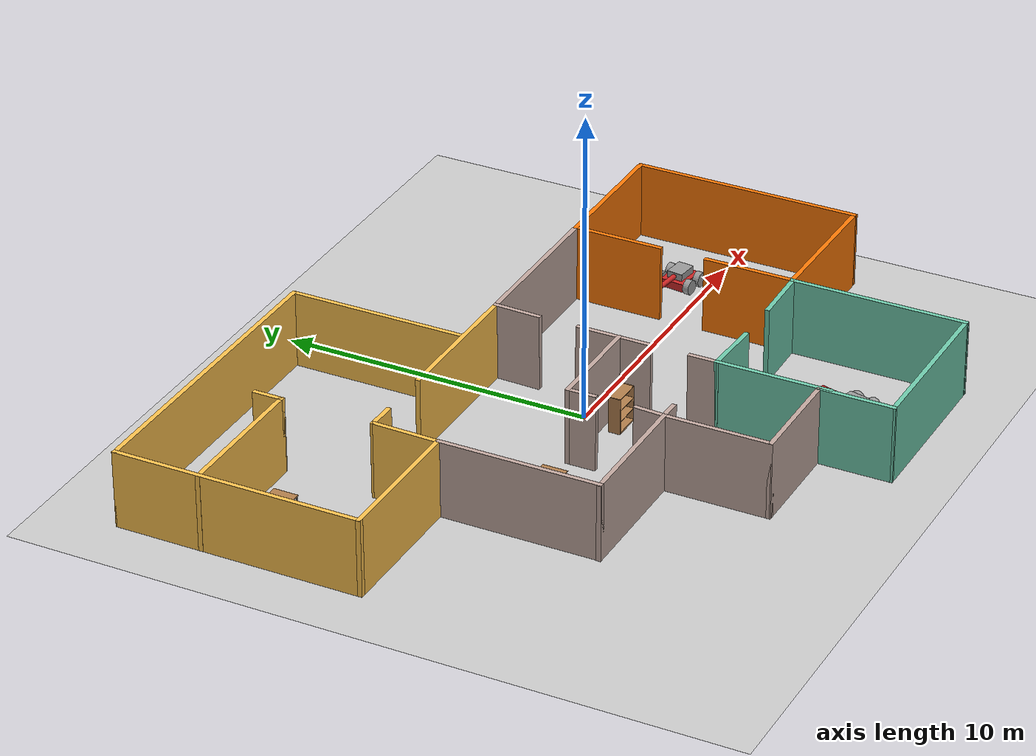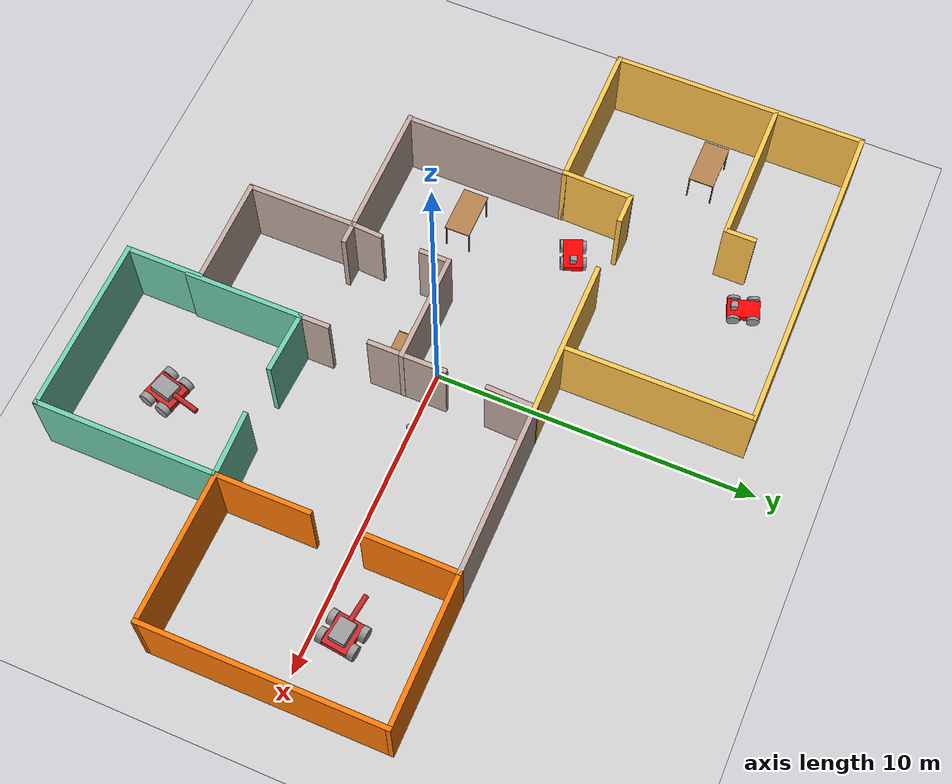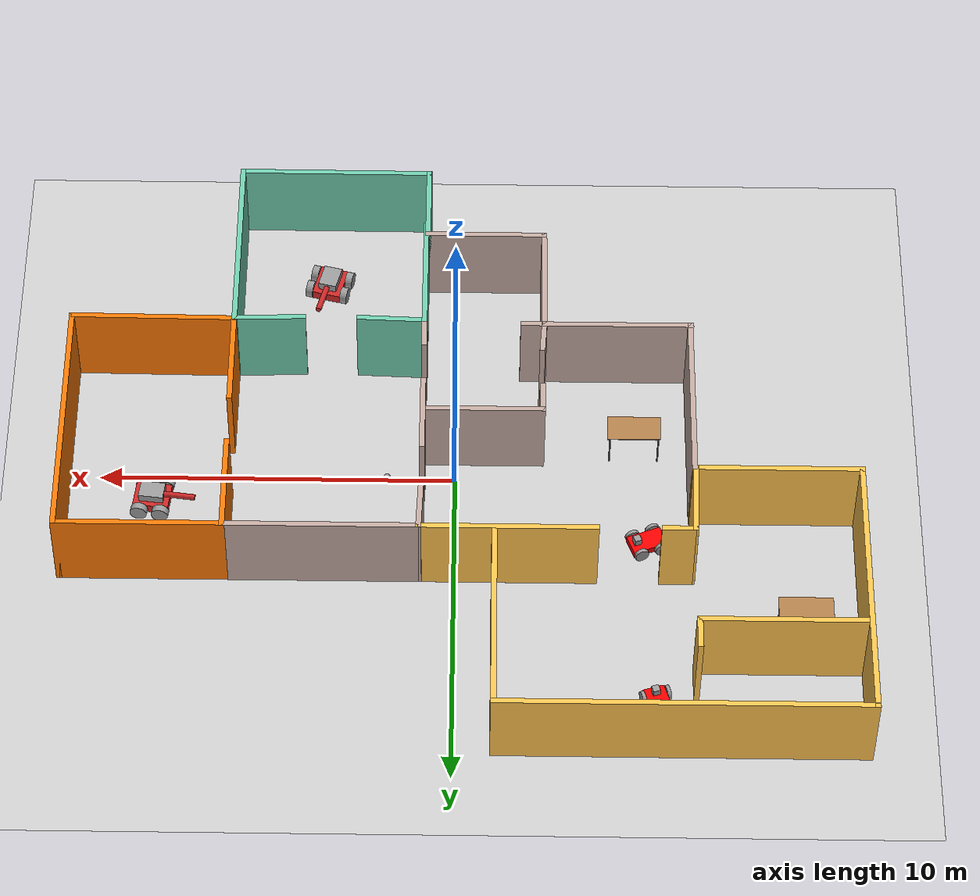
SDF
<sdf version="1.7">
 <world name="default">
  <plugin name="hello" filename="libhello.so"/>
  <light name="sun" type="directional">
   <pose>0 0 10 0 -0 0</pose>
   <diffuse>0.8 0.8 0.8 1</diffuse>
   <specular>0.2 0.2 0.2 1</specular>
   <attenuation>
    <range>1000</range>
    <constant>0.9</constant>
    <linear>0.01</linear>
    <quadratic>0.001</quadratic>
   </attenuation>
   <direction>-0.5 0.1 -0.9</direction>
   <spot><inner_angle>0</inner_angle><outer_angle>0</outer_angle><falloff>0</falloff></spot>
  </light>
  <model name="ground_plane">
   <static>1</static>
   <link name="link">
    <collision name="collision">
     <geometry><plane><normal>0 0 1</normal><size>100 100</size></plane></geometry>
     <surface>
      <contact><collide_bitmask>65535</collide_bitmask></contact>
      <friction><ode><mu>100</mu><mu2>50</mu2></ode></friction>
     </surface>
    </collision>
    <visual name="visual">
     <cast_shadows>0</cast_shadows>
     <geometry><plane><normal>0 0 1</normal><size>100 100</size></plane></geometry>
     <material>
      <script><uri>file://media/materials/scripts/gazebo.material</uri><name>Gazebo/Grey</name></script>
     </material>
    </visual>
   </link>
  </model>
  <gravity>0 0 -9.8</gravity>
  <magnetic_field>6e-06 2.3e-05 -4.2e-05</magnetic_field>
  <atmosphere type="adiabatic"/>
  <physics type="ode">
   <max_step_size>0.001</max_step_size>
   <real_time_factor>1</real_time_factor>
   <real_time_update_rate>1000</real_time_update_rate>
  </physics>
  <scene><ambient>0.4 0.4 0.4 1</ambient><background>0.7 0.7 0.7 1</background><shadows>1</shadows></scene>
  <spherical_coordinates>
   <surface_model>EARTH_WGS84</surface_model>
   <latitude_deg>0</latitude_deg>
   <longitude_deg>0</longitude_deg>
   <elevation>0</elevation>
   <heading_deg>0</heading_deg>
  </spherical_coordinates>
  <model name="MyHome">
   <pose>-0.14512 -0.1471 0 0 -0 0</pose>
   <link name="Wall_0">
    <collision name="Wall_0_Collision">
     <geometry><box><size>5.5 0.15 2.5</size></box></geometry>
     <pose>0 0 1.25 0 -0 0</pose>
    </collision>
    <visual name="Wall_0_Visual">
     <pose>0 0 1.25 0 -0 0</pose>
     <geometry><box><size>5.5 0.15 2.5</size></box></geometry>
     <material>
      <script><uri>file://media/materials/scripts/gazebo.material</uri><name>Gazebo/Grey</name></script>
      <ambient>0.760784 0.662745 0.627451 1</ambient>
     </material>
     <meta><layer>0</layer></meta>
    </visual>
    <pose>3.78803 3.5852 0 0 -0 3.14159</pose>
   </link>
   <link name="Wall_1">
    <collision name="Wall_1_Collision">
     <geometry><box><size>5 0.15 2.5</size></box></geometry>
     <pose>0 0 1.25 0 -0 0</pose>
    </collision>
    <visual name="Wall_1_Visual">
     <pose>0 0 1.25 0 -0 0</pose>
     <geometry><box><size>5 0.15 2.5</size></box></geometry>
     <material>
      <script><uri>file://media/materials/scripts/gazebo.material</uri><name>Gazebo/Grey</name></script>
      <ambient>1 0.764706 0.305882 1</ambient>
     </material>
     <meta><layer>0</layer></meta>
    </visual>
    <pose>-1.31197 3.5852 0 0 -0 3.14159</pose>
   </link>
   <link name="Wall_10">
    <collision name="Wall_10_Collision">
     <geometry><box><size>3.5 0.15 2.5</size></box></geometry>
     <pose>0 0 1.25 0 -0 0</pose>
    </collision>
    <visual name="Wall_10_Visual">
     <pose>0 0 1.25 0 -0 0</pose>
     <geometry><box><size>3.5 0.15 2.5</size></box></geometry>
     <material>
      <script><uri>file://media/materials/scripts/gazebo.material</uri><name>Gazebo/Grey</name></script>
      <ambient>0.760784 0.662745 0.627451 1</ambient>
     </material>
     <meta><layer>0</layer></meta>
    </visual>
    <pose>-0.661974 -6.96481 0 0 -0 0</pose>
   </link>
   <link name="Wall_11">
    <collision name="Wall_11_Collision">
     <geometry><box><size>2.5 0.15 2.5</size></box></geometry>
     <pose>0 0 1.25 0 -0 0</pose>
    </collision>
    <visual name="Wall_11_Visual">
     <pose>0 0 1.25 0 -0 0</pose>
     <geometry><box><size>2.5 0.15 2.5</size></box></geometry>
     <material>
      <script><uri>file://media/materials/scripts/gazebo.material</uri><name>Gazebo/Grey</name></script>
      <ambient>0.435294 0.796078 0.67451 1</ambient>
     </material>
     <meta><layer>0</layer></meta>
    </visual>
    <pose>1.01303 -8.13981 0 0 -0 -1.5708</pose>
   </link>
   <link name="Wall_12">
    <collision name="Wall_12_Collision">
     <geometry><box><size>5.56902 0.15 2.5</size></box></geometry>
     <pose>0 0 1.25 0 -0 0</pose>
    </collision>
    <visual name="Wall_12_Visual">
     <pose>0 0 1.25 0 -0 0</pose>
     <geometry><box><size>5.56902 0.15 2.5</size></box></geometry>
     <material>
      <script><uri>file://media/materials/scripts/gazebo.material</uri><name>Gazebo/Grey</name></script>
      <ambient>0.435294 0.796078 0.67451 1</ambient>
     </material>
     <meta><layer>0</layer></meta>
    </visual>
    <pose>3.72251 -9.32486 0 0 -0 -0.003712</pose>
   </link>
   <link name="Wall_13">
    <collision name="Wall_13_Collision">
     <geometry><box><size>5.75 0.15 2.5</size></box></geometry>
     <pose>0 0 1.25 0 -0 0</pose>
    </collision>
    <visual name="Wall_13_Visual">
     <pose>0 0 1.25 0 -0 0</pose>
     <geometry><box><size>5.75 0.15 2.5</size></box></geometry>
     <material>
      <script><uri>file://media/materials/scripts/gazebo.material</uri><name>Gazebo/Grey</name></script>
      <ambient>0.435294 0.796078 0.67451 1</ambient>
     </material>
     <meta><layer>0</layer></meta>
    </visual>
    <pose>6.45212 -6.53492 0 0 -0 1.5708</pose>
   </link>
   <link name="Wall_14">
    <collision name="Wall_14_Collision">
     <geometry><box><size>2.06964 0.15 2.5</size></box></geometry>
     <pose>0 0 1.25 0 -0 0</pose>
    </collision>
    <visual name="Wall_14_Visual">
     <pose>0 0 1.25 0 -0 0</pose>
     <geometry><box><size>2.06964 0.15 2.5</size></box></geometry>
     <material>
      <script><uri>file://media/materials/scripts/gazebo.material</uri><name>Gazebo/Grey</name></script>
      <ambient>0.435294 0.796078 0.67451 1</ambient>
     </material>
     <meta><layer>0</layer></meta>
    </visual>
    <pose>5.47251 -3.76004 0 0 -0 -3.11542</pose>
   </link>
   <link name="Wall_16">
    <collision name="Wall_16_Collision">
     <geometry><box><size>2.00134 0.15 2.5</size></box></geometry>
     <pose>0 0 1.25 0 -0 0</pose>
    </collision>
    <visual name="Wall_16_Visual">
     <pose>0 0 1.25 0 -0 0</pose>
     <geometry><box><size>2.00134 0.15 2.5</size></box></geometry>
     <material>
      <script><uri>file://media/materials/scripts/gazebo.material</uri><name>Gazebo/Grey</name></script>
      <ambient>0.435294 0.796078 0.67451 1</ambient>
     </material>
     <meta><layer>0</layer></meta>
    </visual>
    <pose>1.98803 -3.74998 0 0 -0 3.10358</pose>
   </link>
   <link name="Wall_17">
    <collision name="Wall_17_Collision">
     <geometry><box><size>3.75 0.15 2.5</size></box></geometry>
     <pose>0 0 1.25 0 -0 0</pose>
    </collision>
    <visual name="Wall_17_Visual">
     <pose>0 0 1.25 0 -0 0</pose>
     <geometry><box><size>3.75 0.15 2.5</size></box></geometry>
     <material>
      <script><uri>file://media/materials/scripts/gazebo.material</uri><name>Gazebo/Grey</name></script>
      <ambient>0.435294 0.796078 0.67451 1</ambient>
     </material>
     <meta><layer>0</layer></meta>
    </visual>
    <pose>1.06303 -5.5148 0 0 -0 -1.5708</pose>
   </link>
   <link name="Wall_19">
    <collision name="Wall_19_Collision">
     <geometry><box><size>0.75 0.15 2.5</size></box></geometry>
     <pose>0 0 1.25 0 -0 0</pose>
    </collision>
    <visual name="Wall_19_Visual">
     <pose>0 0 1.25 0 -0 0</pose>
     <geometry><box><size>0.75 0.15 2.5</size></box></geometry>
     <material>
      <script><uri>file://media/materials/scripts/gazebo.material</uri><name>Gazebo/Grey</name></script>
      <ambient>0.760784 0.662745 0.627451 1</ambient>
     </material>
     <meta><layer>0</layer></meta>
    </visual>
    <pose>-2.03697 -3.61481 0 0 -0 0</pose>
   </link>
   <link name="Wall_23">
    <collision name="Wall_23_Collision">
     <geometry><box><size>1 0.15 2.5</size></box></geometry>
     <pose>0 0 1.25 0 -0 0</pose>
    </collision>
    <visual name="Wall_23_Visual">
     <pose>0 0 1.25 0 -0 0</pose>
     <geometry><box><size>1 0.15 2.5</size></box></geometry>
     <material>
      <script><uri>file://media/materials/scripts/gazebo.material</uri><name>Gazebo/Grey</name></script>
      <ambient>0.760784 0.662745 0.627451 1</ambient>
     </material>
     <meta><layer>0</layer></meta>
    </visual>
    <pose>1.06303 -3.2898 0 0 -0 1.5708</pose>
   </link>
   <link name="Wall_25">
    <collision name="Wall_25_Collision">
     <geometry><box><size>2.45977 0.15 2.5</size></box></geometry>
     <pose>0 0 1.25 0 -0 0</pose>
    </collision>
    <visual name="Wall_25_Visual">
     <pose>0 0 1.25 0 -0 0</pose>
     <geometry><box><size>2.45977 0.15 2.5</size></box></geometry>
     <material>
      <script><uri>file://media/materials/scripts/gazebo.material</uri><name>Gazebo/Grey</name></script>
      <ambient>0.760784 0.662745 0.627451 1</ambient>
     </material>
     <meta><layer>0</layer></meta>
    </visual>
    <pose>1.06303 -0.359918 0 0 -0 1.5708</pose>
   </link>
   <link name="Wall_27">
    <collision name="Wall_27_Collision">
     <geometry><box><size>1.59109 0.15 2.5</size></box></geometry>
     <pose>0 0 1.25 0 -0 0</pose>
    </collision>
    <visual name="Wall_27_Visual">
     <pose>0 0 1.25 0 -0 0</pose>
     <geometry><box><size>1.59109 0.15 2.5</size></box></geometry>
     <material>
      <script><uri>file://media/materials/scripts/gazebo.material</uri><name>Gazebo/Grey</name></script>
      <ambient>0.760784 0.662745 0.627451 1</ambient>
     </material>
     <meta><layer>0</layer></meta>
    </visual>
    <pose>1.08803 2.86508 0 0 -0 1.53609</pose>
   </link>
   <link name="Wall_29">
    <collision name="Wall_29_Collision">
     <geometry><box><size>3.5 0.15 2.5</size></box></geometry>
     <pose>0 0 1.25 0 -0 0</pose>
    </collision>
    <visual name="Wall_29_Visual">
     <pose>0 0 1.25 0 -0 0</pose>
     <geometry><box><size>3.5 0.15 2.5</size></box></geometry>
     <material>
      <script><uri>file://media/materials/scripts/gazebo.material</uri><name>Gazebo/Grey</name></script>
      <ambient>0.760784 0.662745 0.627451 1</ambient>
     </material>
     <meta><layer>0</layer></meta>
    </visual>
    <pose>-0.606876 -0.519992 0 0 -0 3.14159</pose>
   </link>
   <link name="Wall_30">
    <collision name="Wall_30_Collision">
     <geometry><box><size>1 0.15 2.5</size></box></geometry>
     <pose>0 0 1.25 0 -0 0</pose>
    </collision>
    <visual name="Wall_30_Visual">
     <pose>0 0 1.25 0 -0 0</pose>
     <geometry><box><size>1 0.15 2.5</size></box></geometry>
     <material>
      <script><uri>file://media/materials/scripts/gazebo.material</uri><name>Gazebo/Grey</name></script>
      <ambient>0.760784 0.662745 0.627451 1</ambient>
     </material>
     <meta><layer>0</layer></meta>
    </visual>
    <pose>-2.28188 -0.944992 0 0 -0 -1.5708</pose>
   </link>
   <link name="Wall_32">
    <collision name="Wall_32_Collision">
     <geometry><box><size>1.04651 0.15 2.5</size></box></geometry>
     <pose>0 0 1.25 0 -0 0</pose>
    </collision>
    <visual name="Wall_32_Visual">
     <pose>0 0 1.25 0 -0 0</pose>
     <geometry><box><size>1.04651 0.15 2.5</size></box></geometry>
     <material>
      <script><uri>file://media/materials/scripts/gazebo.material</uri><name>Gazebo/Grey</name></script>
      <ambient>0.760784 0.662745 0.627451 1</ambient>
     </material>
     <meta><layer>0</layer></meta>
    </visual>
    <pose>-2.30943 -3.1674 0 0 -0 -1.63229</pose>
   </link>
   <link name="Wall_34">
    <collision name="Wall_34_Collision">
     <geometry><box><size>3 0.15 2.5</size></box></geometry>
     <pose>0 0 1.25 0 -0 0</pose>
    </collision>
    <visual name="Wall_34_Visual">
     <pose>0 0 1.25 0 -0 0</pose>
     <geometry><box><size>3 0.15 2.5</size></box></geometry>
     <material>
      <script><uri>file://media/materials/scripts/gazebo.material</uri><name>Gazebo/Grey</name></script>
      <ambient>0.996078 0.47451 0.0196078 1</ambient>
     </material>
     <meta><layer>0</layer></meta>
    </visual>
    <pose>6.46303 2.16019 0 0 -0 -1.5708</pose>
   </link>
   <link name="Wall_36">
    <collision name="Wall_36_Collision">
     <geometry><box><size>3 0.15 2.5</size></box></geometry>
     <pose>0 0 1.25 0 -0 0</pose>
    </collision>
    <visual name="Wall_36_Visual">
     <pose>0 0 1.25 0 -0 0</pose>
     <geometry><box><size>3 0.15 2.5</size></box></geometry>
     <material>
      <script><uri>file://media/materials/scripts/gazebo.material</uri><name>Gazebo/Grey</name></script>
      <ambient>0.996078 0.47451 0.0196078 1</ambient>
     </material>
     <meta><layer>0</layer></meta>
    </visual>
    <pose>6.46303 -2.2898 0 0 -0 -1.5708</pose>
   </link>
   <link name="Wall_38">
    <collision name="Wall_38_Collision">
     <geometry><box><size>4.75 0.15 2.5</size></box></geometry>
     <pose>0 0 1.25 0 -0 0</pose>
    </collision>
    <visual name="Wall_38_Visual">
     <pose>0 0 1.25 0 -0 0</pose>
     <geometry><box><size>4.75 0.15 2.5</size></box></geometry>
     <material>
      <script><uri>file://media/materials/scripts/gazebo.material</uri><name>Gazebo/Grey</name></script>
      <ambient>0.996078 0.47451 0.0196078 1</ambient>
     </material>
     <meta><layer>0</layer></meta>
    </visual>
    <pose>8.76303 3.5852 0 0 -0 0</pose>
   </link>
   <link name="Wall_39">
    <collision name="Wall_39_Collision">
     <geometry><box><size>7.5 0.15 2.5</size></box></geometry>
     <pose>0 0 1.25 0 -0 0</pose>
    </collision>
    <visual name="Wall_39_Visual">
     <pose>0 0 1.25 0 -0 0</pose>
     <geometry><box><size>7.5 0.15 2.5</size></box></geometry>
     <material>
      <script><uri>file://media/materials/scripts/gazebo.material</uri><name>Gazebo/Grey</name></script>
      <ambient>0.996078 0.47451 0.0196078 1</ambient>
     </material>
     <meta><layer>0</layer></meta>
    </visual>
    <pose>11.063 -0.089805 0 0 -0 -1.5708</pose>
   </link>
   <link name="Wall_4">
    <collision name="Wall_4_Collision">
     <geometry><box><size>2.25 0.15 2.5</size></box></geometry>
     <pose>0 0 1.25 0 -0 0</pose>
    </collision>
    <visual name="Wall_4_Visual">
     <pose>0 0 1.25 0 -0 0</pose>
     <geometry><box><size>2.25 0.15 2.5</size></box></geometry>
     <material>
      <script><uri>file://media/materials/scripts/gazebo.material</uri><name>Gazebo/Grey</name></script>
      <ambient>1 0.764706 0.305882 1</ambient>
     </material>
     <meta><layer>0</layer></meta>
    </visual>
    <pose>-6.46011 2.53519 0 0 -0 -1.59282</pose>
   </link>
   <link name="Wall_40">
    <collision name="Wall_40_Collision">
     <geometry><box><size>4.75027 0.15 2.5</size></box></geometry>
     <pose>0 0 1.25 0 -0 0</pose>
    </collision>
    <visual name="Wall_40_Visual">
     <pose>0 0 1.25 0 -0 0</pose>
     <geometry><box><size>4.75027 0.15 2.5</size></box></geometry>
     <material>
      <script><uri>file://media/materials/scripts/gazebo.material</uri><name>Gazebo/Grey</name></script>
      <ambient>0.996078 0.47451 0.0196078 1</ambient>
     </material>
     <meta><layer>0</layer></meta>
    </visual>
    <pose>8.76303 -3.73981 0 0 -0 3.13072</pose>
   </link>
   <link name="Wall_42">
    <collision name="Wall_42_Collision">
     <geometry><box><size>1 0.15 2.5</size></box></geometry>
     <pose>0 0 1.25 0 -0 0</pose>
    </collision>
    <visual name="Wall_42_Visual">
     <pose>0 0 1.25 0 -0 0</pose>
     <geometry><box><size>1 0.15 2.5</size></box></geometry>
     <material>
      <script><uri>file://media/materials/scripts/gazebo.material</uri><name>Gazebo/Grey</name></script>
      <ambient>1 0.764706 0.305882 1</ambient>
     </material>
     <meta><layer>0</layer></meta>
    </visual>
    <pose>-6.01197 3.5852 0 0 -0 0</pose>
   </link>
   <link name="Wall_44">
    <collision name="Wall_44_Collision">
     <geometry><box><size>4.75 0.15 2.5</size></box></geometry>
     <pose>0 0 1.25 0 -0 0</pose>
    </collision>
    <visual name="Wall_44_Visual">
     <pose>0 0 1.25 0 -0 0</pose>
     <geometry><box><size>4.75 0.15 2.5</size></box></geometry>
     <material>
      <script><uri>file://media/materials/scripts/gazebo.material</uri><name>Gazebo/Grey</name></script>
      <ambient>1 0.764706 0.305882 1</ambient>
     </material>
     <meta><layer>0</layer></meta>
    </visual>
    <pose>-8.7601 1.4852 0 0 -0 3.14159</pose>
   </link>
   <link name="Wall_45">
    <collision name="Wall_45_Collision">
     <geometry><box><size>8 0.15 2.5</size></box></geometry>
     <pose>0 0 1.25 0 -0 0</pose>
    </collision>
    <visual name="Wall_45_Visual">
     <pose>0 0 1.25 0 -0 0</pose>
     <geometry><box><size>8 0.15 2.5</size></box></geometry>
     <material>
      <script><uri>file://media/materials/scripts/gazebo.material</uri><name>Gazebo/Grey</name></script>
      <ambient>1 0.764706 0.305882 1</ambient>
     </material>
     <meta><layer>0</layer></meta>
    </visual>
    <pose>-11.0601 5.41019 0 0 -0 1.5708</pose>
   </link>
   <link name="Wall_46">
    <collision name="Wall_46_Collision">
     <geometry><box><size>10.25 0.15 2.5</size></box></geometry>
     <pose>0 0 1.25 0 -0 0</pose>
    </collision>
    <visual name="Wall_46_Visual">
     <pose>0 0 1.25 0 -0 0</pose>
     <geometry><box><size>10.25 0.15 2.5</size></box></geometry>
     <material>
      <script><uri>file://media/materials/scripts/gazebo.material</uri><name>Gazebo/Grey</name></script>
      <ambient>1 0.764706 0.305882 1</ambient>
     </material>
     <meta><layer>0</layer></meta>
    </visual>
    <pose>-6.01011 9.3352 0 0 -0 0</pose>
   </link>
   <link name="Wall_47">
    <collision name="Wall_47_Collision">
     <geometry><box><size>5.75 0.15 2.5</size></box></geometry>
     <pose>0 0 1.25 0 -0 0</pose>
    </collision>
    <visual name="Wall_47_Visual">
     <pose>0 0 1.25 0 -0 0</pose>
     <geometry><box><size>5.75 0.15 2.5</size></box></geometry>
     <material>
      <script><uri>file://media/materials/scripts/gazebo.material</uri><name>Gazebo/Grey</name></script>
      <ambient>1 0.764706 0.305882 1</ambient>
     </material>
     <meta><layer>0</layer></meta>
    </visual>
    <pose>-0.960105 6.53519 0 0 -0 -1.5708</pose>
   </link>
   <link name="Wall_5">
    <collision name="Wall_5_Collision">
     <geometry><box><size>5.25 0.15 2.5</size></box></geometry>
     <pose>0 0 1.25 0 -0 0</pose>
    </collision>
    <visual name="Wall_5_Visual">
     <pose>0 0 1.25 0 -0 0</pose>
     <geometry><box><size>5.25 0.15 2.5</size></box></geometry>
     <material>
      <script><uri>file://media/materials/scripts/gazebo.material</uri><name>Gazebo/Grey</name></script>
      <ambient>0.760784 0.662745 0.627451 1</ambient>
     </material>
     <meta><layer>0</layer></meta>
    </visual>
    <pose>-6.46011 -1.06481 0 0 -0 -1.5708</pose>
   </link>
   <link name="Wall_50">
    <collision name="Wall_50_Collision">
     <geometry><box><size>4.75 0.15 2.5</size></box></geometry>
     <pose>0 0 1.25 0 -0 0</pose>
    </collision>
    <visual name="Wall_50_Visual">
     <pose>0 0 1.25 0 -0 0</pose>
     <geometry><box><size>4.75 0.15 2.5</size></box></geometry>
     <material>
      <script><uri>file://media/materials/scripts/gazebo.material</uri><name>Gazebo/Grey</name></script>
      <ambient>1 0.764706 0.305882 1</ambient>
     </material>
     <meta><layer>0</layer></meta>
    </visual>
    <pose>-8.76384 6.60144 0 0 -0 0</pose>
   </link>
   <link name="Wall_51">
    <collision name="Wall_51_Collision">
     <geometry><box><size>1 0.15 2.5</size></box></geometry>
     <pose>0 0 1.25 0 -0 0</pose>
    </collision>
    <visual name="Wall_51_Visual">
     <pose>0 0 1.25 0 -0 0</pose>
     <geometry><box><size>1 0.15 2.5</size></box></geometry>
     <material>
      <script><uri>file://media/materials/scripts/gazebo.material</uri><name>Gazebo/Grey</name></script>
      <ambient>1 0.764706 0.305882 1</ambient>
     </material>
     <meta><layer>0</layer></meta>
    </visual>
    <pose>-6.46384 7.02644 0 0 -0 1.5708</pose>
   </link>
   <link name="Wall_8">
    <collision name="Wall_8_Collision">
     <geometry><box><size>4.29626 0.15 2.5</size></box></geometry>
     <pose>0 0 1.25 0 -0 0</pose>
    </collision>
    <visual name="Wall_8_Visual">
     <pose>0 0 1.25 0 -0 0</pose>
     <geometry><box><size>4.29626 0.15 2.5</size></box></geometry>
     <material>
      <script><uri>file://media/materials/scripts/gazebo.material</uri><name>Gazebo/Grey</name></script>
      <ambient>0.760784 0.662745 0.627451 1</ambient>
     </material>
     <meta><layer>0</layer></meta>
    </visual>
    <pose>-4.4101 -3.61481 0 0 -0 0</pose>
   </link>
   <link name="Wall_9">
    <collision name="Wall_9_Collision">
     <geometry><box><size>3.5 0.15 2.5</size></box></geometry>
     <pose>0 0 1.25 0 -0 0</pose>
    </collision>
    <visual name="Wall_9_Visual">
     <pose>0 0 1.25 0 -0 0</pose>
     <geometry><box><size>3.5 0.15 2.5</size></box></geometry>
     <material>
      <script><uri>file://media/materials/scripts/gazebo.material</uri><name>Gazebo/Grey</name></script>
      <ambient>0.760784 0.662745 0.627451 1</ambient>
     </material>
     <meta><layer>0</layer></meta>
    </visual>
    <pose>-2.33697 -5.28981 0 0 -0 -1.5708</pose>
   </link>
   <static>1</static>
  </model>
  <model name="bookshelf">
   <static>1</static>
   <link name="link">
    <inertial><mass>1</mass></inertial>
    <collision name="back">
     <pose>0 0.005 0.6 0 -0 0</pose>
     <geometry><box><size>0.9 0.01 1.2</size></box></geometry>
    </collision>
    <visual name="visual1">
     <pose>0 0.005 0.6 0 -0 0</pose>
     <geometry><box><size>0.9 0.01 1.2</size></box></geometry>
     <material>
      <script><uri>file://media/materials/scripts/gazebo.material</uri><name>Gazebo/Wood</name></script>
     </material>
    </visual>
    <collision name="left_side">
     <pose>0.45 -0.195 0.6 0 -0 0</pose>
     <geometry><box><size>0.02 0.4 1.2</size></box></geometry>
    </collision>
    <visual name="visual2">
     <pose>0.45 -0.195 0.6 0 -0 0</pose>
     <geometry><box><size>0.02 0.4 1.2</size></box></geometry>
     <material>
      <script><uri>file://media/materials/scripts/gazebo.material</uri><name>Gazebo/Wood</name></script>
     </material>
    </visual>
    <collision name="right_side">
     <pose>-0.45 -0.195 0.6 0 -0 0</pose>
     <geometry><box><size>0.02 0.4 1.2</size></box></geometry>
    </collision>
    <visual name="visual3">
     <pose>-0.45 -0.195 0.6 0 -0 0</pose>
     <geometry><box><size>0.02 0.4 1.2</size></box></geometry>
     <material>
      <script><uri>file://media/materials/scripts/gazebo.material</uri><name>Gazebo/Wood</name></script>
     </material>
    </visual>
    <collision name="bottom">
     <pose>0 -0.195 0.03 0 -0 0</pose>
     <geometry><box><size>0.88 0.4 0.06</size></box></geometry>
    </collision>
    <visual name="visual4">
     <pose>0 -0.195 0.03 0 -0 0</pose>
     <geometry><box><size>0.88 0.4 0.06</size></box></geometry>
     <material>
      <script><uri>file://media/materials/scripts/gazebo.material</uri><name>Gazebo/Wood</name></script>
     </material>
    </visual>
    <collision name="top">
     <pose>0 -0.195 1.19 0 -0 0</pose>
     <geometry><box><size>0.88 0.4 0.02</size></box></geometry>
    </collision>
    <visual name="visual5">
     <pose>0 -0.195 1.19 0 -0 0</pose>
     <geometry><box><size>0.88 0.4 0.02</size></box></geometry>
     <material>
      <script><uri>file://media/materials/scripts/gazebo.material</uri><name>Gazebo/Wood</name></script>
     </material>
    </visual>
    <collision name="low_shelf">
     <pose>0 -0.195 0.43 0 -0 0</pose>
     <geometry><box><size>0.88 0.4 0.02</size></box></geometry>
    </collision>
    <visual name="visual6">
     <pose>0 -0.195 0.43 0 -0 0</pose>
     <geometry><box><size>0.88 0.4 0.02</size></box></geometry>
     <material>
      <script><uri>file://media/materials/scripts/gazebo.material</uri><name>Gazebo/Wood</name></script>
     </material>
    </visual>
    <collision name="high_shelf">
     <pose>0 -0.195 0.8 0 -0 0</pose>
     <geometry><box><size>0.88 0.4 0.02</size></box></geometry>
    </collision>
    <visual name="visual7">
     <pose>0 -0.195 0.8 0 -0 0</pose>
     <geometry><box><size>0.88 0.4 0.02</size></box></geometry>
     <material>
      <script><uri>file://media/materials/scripts/gazebo.material</uri><name>Gazebo/Wood</name></script>
     </material>
    </visual>
   </link>
   <pose>0.078975 -0.971396 0 0 -0 0</pose>
  </model>
  <model name="table">
   <static>1</static>
   <link name="link">
    <collision name="surface">
     <pose>0 0 1 0 -0 0</pose>
     <geometry><box><size>1.5 0.8 0.03</size></box></geometry>
     <surface><friction><ode><mu>0.6</mu><mu2>0.6</mu2></ode></friction></surface>
    </collision>
    <visual name="visual1">
     <pose>0 0 1 0 -0 0</pose>
     <geometry><box><size>1.5 0.8 0.03</size></box></geometry>
     <material>
      <script><uri>file://media/materials/scripts/gazebo.material</uri><name>Gazebo/Wood</name></script>
     </material>
    </visual>
    <collision name="front_left_leg">
     <pose>0.68 0.38 0.5 0 -0 0</pose>
     <geometry><cylinder><radius>0.02</radius><length>1</length></cylinder></geometry>
    </collision>
    <visual name="front_left_leg">
     <pose>0.68 0.38 0.5 0 -0 0</pose>
     <geometry><cylinder><radius>0.02</radius><length>1</length></cylinder></geometry>
     <material>
      <script><uri>file://media/materials/scripts/gazebo.material</uri><name>Gazebo/Grey</name></script>
     </material>
    </visual>
    <collision name="front_right_leg">
     <pose>0.68 -0.38 0.5 0 -0 0</pose>
     <geometry><cylinder><radius>0.02</radius><length>1</length></cylinder></geometry>
    </collision>
    <visual name="front_right_leg">
     <pose>0.68 -0.38 0.5 0 -0 0</pose>
     <geometry><cylinder><radius>0.02</radius><length>1</length></cylinder></geometry>
     <material>
      <script><uri>file://media/materials/scripts/gazebo.material</uri><name>Gazebo/Grey</name></script>
     </material>
    </visual>
    <collision name="back_right_leg">
     <pose>-0.68 -0.38 0.5 0 -0 0</pose>
     <geometry><cylinder><radius>0.02</radius><length>1</length></cylinder></geometry>
    </collision>
    <visual name="back_right_leg">
     <pose>-0.68 -0.38 0.5 0 -0 0</pose>
     <geometry><cylinder><radius>0.02</radius><length>1</length></cylinder></geometry>
     <material>
      <script><uri>file://media/materials/scripts/gazebo.material</uri><name>Gazebo/Grey</name></script>
     </material>
    </visual>
    <collision name="back_left_leg">
     <pose>-0.68 0.38 0.5 0 -0 0</pose>
     <geometry><cylinder><radius>0.02</radius><length>1</length></cylinder></geometry>
    </collision>
    <visual name="back_left_leg">
     <pose>-0.68 0.38 0.5 0 -0 0</pose>
     <geometry><cylinder><radius>0.02</radius><length>1</length></cylinder></geometry>
     <material>
      <script><uri>file://media/materials/scripts/gazebo.material</uri><name>Gazebo/Grey</name></script>
     </material>
    </visual>
   </link>
   <pose>-5.03003 -1.20007 0 0 -0 0</pose>
  </model>
  <model name="table_0">
   <static>1</static>
   <link name="link">
    <collision name="surface">
     <pose>0 0 1 0 -0 0</pose>
     <geometry><box><size>1.5 0.8 0.03</size></box></geometry>
     <surface><friction><ode><mu>0.6</mu><mu2>0.6</mu2></ode></friction></surface>
    </collision>
    <visual name="visual1">
     <pose>0 0 1 0 -0 0</pose>
     <geometry><box><size>1.5 0.8 0.03</size></box></geometry>
     <material>
      <script><uri>file://media/materials/scripts/gazebo.material</uri><name>Gazebo/Wood</name></script>
     </material>
    </visual>
    <collision name="front_left_leg">
     <pose>0.68 0.38 0.5 0 -0 0</pose>
     <geometry><cylinder><radius>0.02</radius><length>1</length></cylinder></geometry>
    </collision>
    <visual name="front_left_leg">
     <pose>0.68 0.38 0.5 0 -0 0</pose>
     <geometry><cylinder><radius>0.02</radius><length>1</length></cylinder></geometry>
     <material>
      <script><uri>file://media/materials/scripts/gazebo.material</uri><name>Gazebo/Grey</name></script>
     </material>
    </visual>
    <collision name="front_right_leg">
     <pose>0.68 -0.38 0.5 0 -0 0</pose>
     <geometry><cylinder><radius>0.02</radius><length>1</length></cylinder></geometry>
    </collision>
    <visual name="front_right_leg">
     <pose>0.68 -0.38 0.5 0 -0 0</pose>
     <geometry><cylinder><radius>0.02</radius><length>1</length></cylinder></geometry>
     <material>
      <script><uri>file://media/materials/scripts/gazebo.material</uri><name>Gazebo/Grey</name></script>
     </material>
    </visual>
    <collision name="back_right_leg">
     <pose>-0.68 -0.38 0.5 0 -0 0</pose>
     <geometry><cylinder><radius>0.02</radius><length>1</length></cylinder></geometry>
    </collision>
    <visual name="back_right_leg">
     <pose>-0.68 -0.38 0.5 0 -0 0</pose>
     <geometry><cylinder><radius>0.02</radius><length>1</length></cylinder></geometry>
     <material>
      <script><uri>file://media/materials/scripts/gazebo.material</uri><name>Gazebo/Grey</name></script>
     </material>
    </visual>
    <collision name="back_left_leg">
     <pose>-0.68 0.38 0.5 0 -0 0</pose>
     <geometry><cylinder><radius>0.02</radius><length>1</length></cylinder></geometry>
    </collision>
    <visual name="back_left_leg">
     <pose>-0.68 0.38 0.5 0 -0 0</pose>
     <geometry><cylinder><radius>0.02</radius><length>1</length></cylinder></geometry>
     <material>
      <script><uri>file://media/materials/scripts/gazebo.material</uri><name>Gazebo/Grey</name></script>
     </material>
    </visual>
   </link>
   <pose>-9.61632 5.04374 0 0 -0 0</pose>
  </model>
  <model name="Normal_Turtlebot">
   <link name="link_0">
    <inertial>
     <mass>1</mass>
     <inertia>
      <ixx>0.166667</ixx>
      <ixy>0</ixy>
      <ixz>0</ixz>
      <iyy>0.166667</iyy>
      <iyz>0</iyz>
      <izz>0.166667</izz>
     </inertia>
    </inertial>
    <pose>0.016667 0 -0.034708 0 -0 0</pose>
    <visual name="visual">
     <geometry><box><size>1 0.6 0.2</size></box></geometry>
     <material>
      <lighting>1</lighting>
      <script><uri>file://media/materials/scripts/gazebo.material</uri><name>Gazebo/Grey</name></script>
      <shader type="pixel"><normal_map>__default__</normal_map></shader>
      <ambient>1 0 0 1</ambient>
      <diffuse>1 0 0 1</diffuse>
      <specular>0.1 0.1 0.1 1</specular>
      <emissive>0 0 0 1</emissive>
     </material>
    </visual>
    <collision name="collision">
     <geometry><box><size>1 0.6 0.2</size></box></geometry>
     <surface>
      <friction>
       <ode><mu>1</mu><mu2>1</mu2><fdir1>0 0 0</fdir1><slip1>0</slip1><slip2>0</slip2></ode>
       <torsional>
        <coefficient>1</coefficient>
        <patch_radius>0</patch_radius>
        <surface_radius>0</surface_radius>
        <use_patch_radius>1</use_patch_radius>
        <ode><slip>0</slip></ode>
       </torsional>
      </friction>
      <bounce><restitution_coefficient>0</restitution_coefficient><threshold>1e+06</threshold></bounce>
      <contact>
       <collide_without_contact>0</collide_without_contact>
       <collide_without_contact_bitmask>1</collide_without_contact_bitmask>
       <collide_bitmask>1</collide_bitmask>
       <ode>
        <soft_cfm>0</soft_cfm>
        <soft_erp>0.2</soft_erp>
        <kp>1e+13</kp>
        <kd>1</kd>
        <max_vel>0.01</max_vel>
        <min_depth>0</min_depth>
       </ode>
       <bullet>
        <split_impulse>1</split_impulse>
        <split_impulse_penetration_threshold>-0.01</split_impulse_penetration_threshold>
        <soft_cfm>0</soft_cfm>
        <soft_erp>0.2</soft_erp>
        <kp>1e+13</kp>
        <kd>1</kd>
       </bullet>
      </contact>
     </surface>
    </collision>
   </link>
   <link name="link_1">
    <inertial>
     <mass>1</mass>
     <inertia><ixx>0.145833</ixx><ixy>0</ixy><ixz>0</ixz><iyy>0.145833</iyy><iyz>0</iyz><izz>0.125</izz></inertia>
    </inertial>
    <pose>-0.283333 -0.350019 -0.014712 1.5707 -0 0</pose>
    <visual name="visual">
     <geometry><cylinder><radius>0.2</radius><length>0.1</length></cylinder></geometry>
     <material>
      <lighting>1</lighting>
      <script><uri>file://media/materials/scripts/gazebo.material</uri><name>Gazebo/Grey</name></script>
      <shader type="pixel"><normal_map>__default__</normal_map></shader>
      <ambient>0.3 0.3 0.3 1</ambient>
      <diffuse>0.7 0.7 0.7 1</diffuse>
      <specular>0.01 0.01 0.01 1</specular>
      <emissive>0 0 0 1</emissive>
     </material>
    </visual>
    <collision name="collision">
     <geometry><cylinder><radius>0.2</radius><length>0.1</length></cylinder></geometry>
     <surface>
      <friction>
       <ode><mu>1</mu><mu2>1</mu2><fdir1>0 0 0</fdir1><slip1>0</slip1><slip2>0</slip2></ode>
       <torsional>
        <coefficient>1</coefficient>
        <patch_radius>0</patch_radius>
        <surface_radius>0</surface_radius>
        <use_patch_radius>1</use_patch_radius>
        <ode><slip>0</slip></ode>
       </torsional>
      </friction>
      <bounce><restitution_coefficient>0</restitution_coefficient><threshold>1e+06</threshold></bounce>
      <contact>
       <collide_without_contact>0</collide_without_contact>
       <collide_without_contact_bitmask>1</collide_without_contact_bitmask>
       <collide_bitmask>1</collide_bitmask>
       <ode>
        <soft_cfm>0</soft_cfm>
        <soft_erp>0.2</soft_erp>
        <kp>1e+13</kp>
        <kd>1</kd>
        <max_vel>0.01</max_vel>
        <min_depth>0</min_depth>
       </ode>
       <bullet>
        <split_impulse>1</split_impulse>
        <split_impulse_penetration_threshold>-0.01</split_impulse_penetration_threshold>
        <soft_cfm>0</soft_cfm>
        <soft_erp>0.2</soft_erp>
        <kp>1e+13</kp>
        <kd>1</kd>
       </bullet>
      </contact>
     </surface>
    </collision>
   </link>
   <link name="link_1_clone">
    <inertial>
     <mass>1</mass>
     <inertia><ixx>0.145833</ixx><ixy>0</ixy><ixz>0</ixz><iyy>0.145833</iyy><iyz>0</iyz><izz>0.125</izz></inertia>
    </inertial>
    <pose>-0.283333 0.350019 -0.034708 1.5707 -0 0</pose>
    <visual name="visual">
     <geometry><cylinder><radius>0.2</radius><length>0.1</length></cylinder></geometry>
     <material>
      <lighting>1</lighting>
      <script><uri>file://media/materials/scripts/gazebo.material</uri><name>Gazebo/Grey</name></script>
      <shader type="pixel"><normal_map>__default__</normal_map></shader>
      <ambient>0.3 0.3 0.3 1</ambient>
      <diffuse>0.7 0.7 0.7 1</diffuse>
      <specular>0.01 0.01 0.01 1</specular>
      <emissive>0 0 0 1</emissive>
     </material>
    </visual>
    <collision name="collision">
     <geometry><cylinder><radius>0.2</radius><length>0.1</length></cylinder></geometry>
     <surface>
      <friction>
       <ode><mu>1</mu><mu2>1</mu2><fdir1>0 0 0</fdir1><slip1>0</slip1><slip2>0</slip2></ode>
       <torsional>
        <coefficient>1</coefficient>
        <patch_radius>0</patch_radius>
        <surface_radius>0</surface_radius>
        <use_patch_radius>1</use_patch_radius>
        <ode><slip>0</slip></ode>
       </torsional>
      </friction>
      <bounce><restitution_coefficient>0</restitution_coefficient><threshold>1e+06</threshold></bounce>
      <contact>
       <collide_without_contact>0</collide_without_contact>
       <collide_without_contact_bitmask>1</collide_without_contact_bitmask>
       <collide_bitmask>1</collide_bitmask>
       <ode>
        <soft_cfm>0</soft_cfm>
        <soft_erp>0.2</soft_erp>
        <kp>1e+13</kp>
        <kd>1</kd>
        <max_vel>0.01</max_vel>
        <min_depth>0</min_depth>
       </ode>
       <bullet>
        <split_impulse>1</split_impulse>
        <split_impulse_penetration_threshold>-0.01</split_impulse_penetration_threshold>
        <soft_cfm>0</soft_cfm>
        <soft_erp>0.2</soft_erp>
        <kp>1e+13</kp>
        <kd>1</kd>
       </bullet>
      </contact>
     </surface>
    </collision>
   </link>
   <link name="link_1_clone_0">
    <inertial>
     <mass>1</mass>
     <inertia><ixx>0.145833</ixx><ixy>0</ixy><ixz>0</ixz><iyy>0.145833</iyy><iyz>0</iyz><izz>0.125</izz></inertia>
    </inertial>
    <pose>0.316667 0.350019 -0.034708 1.5707 -0 0</pose>
    <visual name="visual">
     <geometry><cylinder><radius>0.2</radius><length>0.1</length></cylinder></geometry>
     <material>
      <lighting>1</lighting>
      <script><uri>file://media/materials/scripts/gazebo.material</uri><name>Gazebo/Grey</name></script>
      <shader type="pixel"><normal_map>__default__</normal_map></shader>
      <ambient>0.3 0.3 0.3 1</ambient>
      <diffuse>0.7 0.7 0.7 1</diffuse>
      <specular>0.01 0.01 0.01 1</specular>
      <emissive>0 0 0 1</emissive>
     </material>
    </visual>
    <collision name="collision">
     <geometry><cylinder><radius>0.2</radius><length>0.1</length></cylinder></geometry>
     <surface>
      <friction>
       <ode><mu>1</mu><mu2>1</mu2><fdir1>0 0 0</fdir1><slip1>0</slip1><slip2>0</slip2></ode>
       <torsional>
        <coefficient>1</coefficient>
        <patch_radius>0</patch_radius>
        <surface_radius>0</surface_radius>
        <use_patch_radius>1</use_patch_radius>
        <ode><slip>0</slip></ode>
       </torsional>
      </friction>
      <bounce><restitution_coefficient>0</restitution_coefficient><threshold>1e+06</threshold></bounce>
      <contact>
       <collide_without_contact>0</collide_without_contact>
       <collide_without_contact_bitmask>1</collide_without_contact_bitmask>
       <collide_bitmask>1</collide_bitmask>
       <ode>
        <soft_cfm>0</soft_cfm>
        <soft_erp>0.2</soft_erp>
        <kp>1e+13</kp>
        <kd>1</kd>
        <max_vel>0.01</max_vel>
        <min_depth>0</min_depth>
       </ode>
       <bullet>
        <split_impulse>1</split_impulse>
        <split_impulse_penetration_threshold>-0.01</split_impulse_penetration_threshold>
        <soft_cfm>0</soft_cfm>
        <soft_erp>0.2</soft_erp>
        <kp>1e+13</kp>
        <kd>1</kd>
       </bullet>
      </contact>
     </surface>
    </collision>
   </link>
   <link name="link_1_clone_1">
    <inertial>
     <mass>1</mass>
     <inertia><ixx>0.145833</ixx><ixy>0</ixy><ixz>0</ixz><iyy>0.145833</iyy><iyz>0</iyz><izz>0.125</izz></inertia>
    </inertial>
    <pose>0.316667 -0.350019 -0.034708 1.5707 -0 0</pose>
    <visual name="visual">
     <geometry><cylinder><radius>0.2</radius><length>0.1</length></cylinder></geometry>
     <material>
      <lighting>1</lighting>
      <script><uri>file://media/materials/scripts/gazebo.material</uri><name>Gazebo/Grey</name></script>
      <shader type="pixel"><normal_map>__default__</normal_map></shader>
      <ambient>0.3 0.3 0.3 1</ambient>
      <diffuse>0.7 0.7 0.7 1</diffuse>
      <specular>0.01 0.01 0.01 1</specular>
      <emissive>0 0 0 1</emissive>
     </material>
    </visual>
    <collision name="collision">
     <geometry><cylinder><radius>0.2</radius><length>0.1</length></cylinder></geometry>
     <surface>
      <friction>
       <ode><mu>1</mu><mu2>1</mu2><fdir1>0 0 0</fdir1><slip1>0</slip1><slip2>0</slip2></ode>
       <torsional>
        <coefficient>1</coefficient>
        <patch_radius>0</patch_radius>
        <surface_radius>0</surface_radius>
        <use_patch_radius>1</use_patch_radius>
        <ode><slip>0</slip></ode>
       </torsional>
      </friction>
      <bounce><restitution_coefficient>0</restitution_coefficient><threshold>1e+06</threshold></bounce>
      <contact>
       <collide_without_contact>0</collide_without_contact>
       <collide_without_contact_bitmask>1</collide_without_contact_bitmask>
       <collide_bitmask>1</collide_bitmask>
       <ode>
        <soft_cfm>0</soft_cfm>
        <soft_erp>0.2</soft_erp>
        <kp>1e+13</kp>
        <kd>1</kd>
        <max_vel>0.01</max_vel>
        <min_depth>0</min_depth>
       </ode>
       <bullet>
        <split_impulse>1</split_impulse>
        <split_impulse_penetration_threshold>-0.01</split_impulse_penetration_threshold>
        <soft_cfm>0</soft_cfm>
        <soft_erp>0.2</soft_erp>
        <kp>1e+13</kp>
        <kd>1</kd>
       </bullet>
      </contact>
     </surface>
    </collision>
   </link>
   <link name="link_2">
    <inertial>
     <mass>0.0103468</mass>
     <inertia>
      <ixx>7.075e-05</ixx>
      <ixy>0</ixy>
      <ixz>0</ixz>
      <iyy>9.168e-05</iyy>
      <iyz>0</iyz>
      <izz>8.896e-05</izz>
     </inertia>
    </inertial>
    <pose>0.316667 2.2e-05 0.205409 0 -0 0</pose>
    <visual name="visual">
     <geometry><box><size>0.2 0.2 0.2</size></box></geometry>
     <material>
      <lighting>1</lighting>
      <script><uri>file://media/materials/scripts/gazebo.material</uri><name>Gazebo/Grey</name></script>
      <shader type="pixel"><normal_map>__default__</normal_map></shader>
      <ambient>0.3 0.3 0.3 1</ambient>
      <diffuse>0.7 0.7 0.7 1</diffuse>
      <specular>0.01 0.01 0.01 1</specular>
      <emissive>0 0 0 1</emissive>
     </material>
    </visual>
    <collision name="collision">
     <geometry><box><size>0.2 0.2 0.2</size></box></geometry>
     <surface>
      <friction>
       <ode><mu>1</mu><mu2>1</mu2><fdir1>0 0 0</fdir1><slip1>0</slip1><slip2>0</slip2></ode>
       <torsional>
        <coefficient>1</coefficient>
        <patch_radius>0</patch_radius>
        <surface_radius>0</surface_radius>
        <use_patch_radius>1</use_patch_radius>
        <ode><slip>0</slip></ode>
       </torsional>
      </friction>
      <bounce><restitution_coefficient>0</restitution_coefficient><threshold>1e+06</threshold></bounce>
      <contact>
       <collide_without_contact>0</collide_without_contact>
       <collide_without_contact_bitmask>1</collide_without_contact_bitmask>
       <collide_bitmask>1</collide_bitmask>
       <ode>
        <soft_cfm>0</soft_cfm>
        <soft_erp>0.2</soft_erp>
        <kp>1e+13</kp>
        <kd>1</kd>
        <max_vel>0.01</max_vel>
        <min_depth>0</min_depth>
       </ode>
       <bullet>
        <split_impulse>1</split_impulse>
        <split_impulse_penetration_threshold>-0.01</split_impulse_penetration_threshold>
        <soft_cfm>0</soft_cfm>
        <soft_erp>0.2</soft_erp>
        <kp>1e+13</kp>
        <kd>1</kd>
       </bullet>
      </contact>
     </surface>
    </collision>
   </link>
   <joint name="link_0_JOINT_0_0" type="fixed">
    <parent>link_0</parent>
    <child>link_2</child>
    <pose>0 0 0 -0.01 0 0</pose>
    <physics>
     <ode><limit><cfm>0</cfm><erp>0.2</erp></limit><suspension><cfm>0</cfm><erp>0.2</erp></suspension></ode>
    </physics>
   </joint>
   <joint name="link_0_JOINT_0" type="revolute">
    <parent>link_0</parent>
    <child>link_1</child>
    <axis>
     <xyz>0 0 1</xyz>
     <limit>
      <lower>-1.79769e+308</lower>
      <upper>1.79769e+308</upper>
      <effort>-1</effort>
      <velocity>-1</velocity>
     </limit>
     <dynamics>
      <spring_reference>0</spring_reference>
      <spring_stiffness>0</spring_stiffness>
      <damping>0</damping>
      <friction>0</friction>
     </dynamics>
    </axis>
    <physics>
     <ode><limit><cfm>0</cfm><erp>0.2</erp></limit><suspension><cfm>0</cfm><erp>0.2</erp></suspension></ode>
    </physics>
   </joint>
   <joint name="link_0_JOINT_1" type="revolute">
    <parent>link_0</parent>
    <child>link_1_clone_1</child>
    <axis>
     <xyz>0 0 1</xyz>
     <limit>
      <lower>-1.79769e+308</lower>
      <upper>1.79769e+308</upper>
      <effort>-1</effort>
      <velocity>-1</velocity>
     </limit>
     <dynamics>
      <spring_reference>0</spring_reference>
      <spring_stiffness>0</spring_stiffness>
      <damping>0</damping>
      <friction>0</friction>
     </dynamics>
    </axis>
    <physics>
     <ode><limit><cfm>0</cfm><erp>0.2</erp></limit><suspension><cfm>0</cfm><erp>0.2</erp></suspension></ode>
    </physics>
   </joint>
   <joint name="link_0_JOINT_2" type="revolute">
    <parent>link_0</parent>
    <child>link_1_clone</child>
    <axis>
     <xyz>0 0 1</xyz>
     <limit>
      <lower>-1.79769e+308</lower>
      <upper>1.79769e+308</upper>
      <effort>-1</effort>
      <velocity>-1</velocity>
     </limit>
     <dynamics>
      <spring_reference>0</spring_reference>
      <spring_stiffness>0</spring_stiffness>
      <damping>0</damping>
      <friction>0</friction>
     </dynamics>
    </axis>
    <physics>
     <ode><limit><cfm>0</cfm><erp>0.2</erp></limit><suspension><cfm>0</cfm><erp>0.2</erp></suspension></ode>
    </physics>
   </joint>
   <joint name="link_0_JOINT_3" type="revolute">
    <parent>link_0</parent>
    <child>link_1_clone_0</child>
    <axis>
     <xyz>0 0 1</xyz>
     <limit>
      <lower>-1.79769e+308</lower>
      <upper>1.79769e+308</upper>
      <effort>-1</effort>
      <velocity>-1</velocity>
     </limit>
     <dynamics>
      <spring_reference>0</spring_reference>
      <spring_stiffness>0</spring_stiffness>
      <damping>0</damping>
      <friction>0</friction>
     </dynamics>
    </axis>
    <physics>
     <ode><limit><cfm>0</cfm><erp>0.2</erp></limit><suspension><cfm>0</cfm><erp>0.2</erp></suspension></ode>
    </physics>
   </joint>
   <static>0</static>
   <pose>-5.38094 2.20899 0.2347 9.8e-05 -0.000117 0.37514</pose>
  </model>
  <model name="Tank_Turtlebot">
   <link name="link_0">
    <inertial>
     <mass>0.21345</mass>
     <inertia>
      <ixx>0.0128699</ixx>
      <ixy>0</ixy>
      <ixz>0</ixz>
      <iyy>0.019027</iyy>
      <iyz>0</iyz>
      <izz>0.0294179</izz>
     </inertia>
    </inertial>
    <pose>-0.154284 0.004173 -0.074722 0 -0 0</pose>
    <visual name="visual">
     <geometry><box><size>1 0.80861 0.263974</size></box></geometry>
     <material>
      <lighting>1</lighting>
      <script><uri>file://media/materials/scripts/gazebo.material</uri><name>Gazebo/Red</name></script>
      <shader type="pixel"><normal_map>__default__</normal_map></shader>
      <ambient>0.157 0.267 0.671 1</ambient>
      <diffuse>0.157 0.267 0.671 1</diffuse>
      <specular>0.1 0.1 0.1 1</specular>
      <emissive>0 0 0 1</emissive>
     </material>
    </visual>
    <collision name="collision">
     <geometry><box><size>1 0.80861 0.263974</size></box></geometry>
     <surface>
      <friction>
       <ode><mu>1</mu><mu2>1</mu2><fdir1>0 0 0</fdir1><slip1>0</slip1><slip2>0</slip2></ode>
       <torsional>
        <coefficient>1</coefficient>
        <patch_radius>0</patch_radius>
        <surface_radius>0</surface_radius>
        <use_patch_radius>1</use_patch_radius>
        <ode><slip>0</slip></ode>
       </torsional>
      </friction>
      <bounce><restitution_coefficient>0</restitution_coefficient><threshold>1e+06</threshold></bounce>
      <contact>
       <collide_without_contact>0</collide_without_contact>
       <collide_without_contact_bitmask>1</collide_without_contact_bitmask>
       <collide_bitmask>1</collide_bitmask>
       <ode>
        <soft_cfm>0</soft_cfm>
        <soft_erp>0.2</soft_erp>
        <kp>1e+13</kp>
        <kd>1</kd>
        <max_vel>0.01</max_vel>
        <min_depth>0</min_depth>
       </ode>
       <bullet>
        <split_impulse>1</split_impulse>
        <split_impulse_penetration_threshold>-0.01</split_impulse_penetration_threshold>
        <soft_cfm>0</soft_cfm>
        <soft_erp>0.2</soft_erp>
        <kp>1e+13</kp>
        <kd>1</kd>
       </bullet>
      </contact>
     </surface>
    </collision>
   </link>
   <link name="link_1">
    <inertial>
     <mass>0.0446444</mass>
     <inertia>
      <ixx>0.00077292</ixx>
      <ixy>0</ixy>
      <ixz>0</ixz>
      <iyy>0.00077292</iyy>
      <iyz>0</iyz>
      <izz>0.00125049</izz>
     </inertia>
    </inertial>
    <pose>-0.454284 -0.503605 -0.070717 1.5707 -0 0</pose>
    <visual name="visual">
     <geometry><cylinder><radius>0.236685</radius><length>0.199236</length></cylinder></geometry>
     <material>
      <lighting>1</lighting>
      <script><uri>file://media/materials/scripts/gazebo.material</uri><name>Gazebo/Grey</name></script>
      <shader type="pixel"><normal_map>__default__</normal_map></shader>
      <ambient>0.3 0.3 0.3 1</ambient>
      <diffuse>0.7 0.7 0.7 1</diffuse>
      <specular>0.01 0.01 0.01 1</specular>
      <emissive>0 0 0 1</emissive>
     </material>
    </visual>
    <collision name="collision">
     <geometry><cylinder><radius>0.236685</radius><length>0.199236</length></cylinder></geometry>
     <surface>
      <friction>
       <ode><mu>1</mu><mu2>1</mu2><fdir1>0 0 0</fdir1><slip1>0</slip1><slip2>0</slip2></ode>
       <torsional>
        <coefficient>1</coefficient>
        <patch_radius>0</patch_radius>
        <surface_radius>0</surface_radius>
        <use_patch_radius>1</use_patch_radius>
        <ode><slip>0</slip></ode>
       </torsional>
      </friction>
      <bounce><restitution_coefficient>0</restitution_coefficient><threshold>1e+06</threshold></bounce>
      <contact>
       <collide_without_contact>0</collide_without_contact>
       <collide_without_contact_bitmask>1</collide_without_contact_bitmask>
       <collide_bitmask>1</collide_bitmask>
       <ode>
        <soft_cfm>0</soft_cfm>
        <soft_erp>0.2</soft_erp>
        <kp>1e+13</kp>
        <kd>1</kd>
        <max_vel>0.01</max_vel>
        <min_depth>0</min_depth>
       </ode>
       <bullet>
        <split_impulse>1</split_impulse>
        <split_impulse_penetration_threshold>-0.01</split_impulse_penetration_threshold>
        <soft_cfm>0</soft_cfm>
        <soft_erp>0.2</soft_erp>
        <kp>1e+13</kp>
        <kd>1</kd>
       </bullet>
      </contact>
     </surface>
    </collision>
   </link>
   <link name="link_1_clone">
    <inertial>
     <mass>0.0446444</mass>
     <inertia>
      <ixx>0.000772923</ixx>
      <ixy>0</ixy>
      <ixz>0</ixz>
      <iyy>0.000772923</iyy>
      <iyz>0</iyz>
      <izz>0.00125049</izz>
     </inertia>
    </inertial>
    <pose>0.145716 -0.503605 -0.070717 1.5707 -0 0</pose>
    <visual name="visual">
     <geometry><cylinder><radius>0.236685</radius><length>0.199236</length></cylinder></geometry>
     <material>
      <lighting>1</lighting>
      <script><uri>file://media/materials/scripts/gazebo.material</uri><name>Gazebo/Grey</name></script>
      <shader type="pixel"><normal_map>__default__</normal_map></shader>
      <ambient>0.3 0.3 0.3 1</ambient>
      <diffuse>0.7 0.7 0.7 1</diffuse>
      <specular>0.01 0.01 0.01 1</specular>
      <emissive>0 0 0 1</emissive>
     </material>
    </visual>
    <collision name="collision">
     <geometry><cylinder><radius>0.236685</radius><length>0.199236</length></cylinder></geometry>
     <surface>
      <friction>
       <ode><mu>1</mu><mu2>1</mu2><fdir1>0 0 0</fdir1><slip1>0</slip1><slip2>0</slip2></ode>
       <torsional>
        <coefficient>1</coefficient>
        <patch_radius>0</patch_radius>
        <surface_radius>0</surface_radius>
        <use_patch_radius>1</use_patch_radius>
        <ode><slip>0</slip></ode>
       </torsional>
      </friction>
      <bounce><restitution_coefficient>0</restitution_coefficient><threshold>1e+06</threshold></bounce>
      <contact>
       <collide_without_contact>0</collide_without_contact>
       <collide_without_contact_bitmask>1</collide_without_contact_bitmask>
       <collide_bitmask>1</collide_bitmask>
       <ode>
        <soft_cfm>0</soft_cfm>
        <soft_erp>0.2</soft_erp>
        <kp>1e+13</kp>
        <kd>1</kd>
        <max_vel>0.01</max_vel>
        <min_depth>0</min_depth>
       </ode>
       <bullet>
        <split_impulse>1</split_impulse>
        <split_impulse_penetration_threshold>-0.01</split_impulse_penetration_threshold>
        <soft_cfm>0</soft_cfm>
        <soft_erp>0.2</soft_erp>
        <kp>1e+13</kp>
        <kd>1</kd>
       </bullet>
      </contact>
     </surface>
    </collision>
   </link>
   <link name="link_1_clone_0">
    <inertial>
     <mass>0.0446444</mass>
     <inertia>
      <ixx>0.000772923</ixx>
      <ixy>0</ixy>
      <ixz>0</ixz>
      <iyy>0.000772923</iyy>
      <iyz>0</iyz>
      <izz>0.00125049</izz>
     </inertia>
    </inertial>
    <pose>0.145716 0.51195 -0.070716 1.5707 -0 0</pose>
    <visual name="visual">
     <geometry><cylinder><radius>0.236685</radius><length>0.199236</length></cylinder></geometry>
     <material>
      <lighting>1</lighting>
      <script><uri>file://media/materials/scripts/gazebo.material</uri><name>Gazebo/Grey</name></script>
      <shader type="pixel"><normal_map>__default__</normal_map></shader>
      <ambient>0.3 0.3 0.3 1</ambient>
      <diffuse>0.7 0.7 0.7 1</diffuse>
      <specular>0.01 0.01 0.01 1</specular>
      <emissive>0 0 0 1</emissive>
     </material>
    </visual>
    <collision name="collision">
     <geometry><cylinder><radius>0.236685</radius><length>0.199236</length></cylinder></geometry>
     <surface>
      <friction>
       <ode><mu>1</mu><mu2>1</mu2><fdir1>0 0 0</fdir1><slip1>0</slip1><slip2>0</slip2></ode>
       <torsional>
        <coefficient>1</coefficient>
        <patch_radius>0</patch_radius>
        <surface_radius>0</surface_radius>
        <use_patch_radius>1</use_patch_radius>
        <ode><slip>0</slip></ode>
       </torsional>
      </friction>
      <bounce><restitution_coefficient>0</restitution_coefficient><threshold>1e+06</threshold></bounce>
      <contact>
       <collide_without_contact>0</collide_without_contact>
       <collide_without_contact_bitmask>1</collide_without_contact_bitmask>
       <collide_bitmask>1</collide_bitmask>
       <ode>
        <soft_cfm>0</soft_cfm>
        <soft_erp>0.2</soft_erp>
        <kp>1e+13</kp>
        <kd>1</kd>
        <max_vel>0.01</max_vel>
        <min_depth>0</min_depth>
       </ode>
       <bullet>
        <split_impulse>1</split_impulse>
        <split_impulse_penetration_threshold>-0.01</split_impulse_penetration_threshold>
        <soft_cfm>0</soft_cfm>
        <soft_erp>0.2</soft_erp>
        <kp>1e+13</kp>
        <kd>1</kd>
       </bullet>
      </contact>
     </surface>
    </collision>
   </link>
   <link name="link_1_clone_1">
    <inertial>
     <mass>0.0446444</mass>
     <inertia>
      <ixx>0.000772923</ixx>
      <ixy>0</ixy>
      <ixz>0</ixz>
      <iyy>0.000772923</iyy>
      <iyz>0</iyz>
      <izz>0.00125049</izz>
     </inertia>
    </inertial>
    <pose>-0.451249 0.510413 -0.070717 1.5707 -0 0</pose>
    <visual name="visual">
     <geometry><cylinder><radius>0.236685</radius><length>0.199236</length></cylinder></geometry>
     <material>
      <lighting>1</lighting>
      <script><uri>file://media/materials/scripts/gazebo.material</uri><name>Gazebo/Grey</name></script>
      <shader type="pixel"><normal_map>__default__</normal_map></shader>
      <ambient>0.3 0.3 0.3 1</ambient>
      <diffuse>0.7 0.7 0.7 1</diffuse>
      <specular>0.01 0.01 0.01 1</specular>
      <emissive>0 0 0 1</emissive>
     </material>
    </visual>
    <collision name="collision">
     <geometry><cylinder><radius>0.236685</radius><length>0.199236</length></cylinder></geometry>
     <surface>
      <friction>
       <ode><mu>1</mu><mu2>1</mu2><fdir1>0 0 0</fdir1><slip1>0</slip1><slip2>0</slip2></ode>
       <torsional>
        <coefficient>1</coefficient>
        <patch_radius>0</patch_radius>
        <surface_radius>0</surface_radius>
        <use_patch_radius>1</use_patch_radius>
        <ode><slip>0</slip></ode>
       </torsional>
      </friction>
      <bounce><restitution_coefficient>0</restitution_coefficient><threshold>1e+06</threshold></bounce>
      <contact>
       <collide_without_contact>0</collide_without_contact>
       <collide_without_contact_bitmask>1</collide_without_contact_bitmask>
       <collide_bitmask>1</collide_bitmask>
       <ode>
        <soft_cfm>0</soft_cfm>
        <soft_erp>0.2</soft_erp>
        <kp>1e+13</kp>
        <kd>1</kd>
        <max_vel>0.01</max_vel>
        <min_depth>0</min_depth>
       </ode>
       <bullet>
        <split_impulse>1</split_impulse>
        <split_impulse_penetration_threshold>-0.01</split_impulse_penetration_threshold>
        <soft_cfm>0</soft_cfm>
        <soft_erp>0.2</soft_erp>
        <kp>1e+13</kp>
        <kd>1</kd>
       </bullet>
      </contact>
     </surface>
    </collision>
   </link>
   <link name="link_2">
    <inertial>
     <mass>0.0852707</mass>
     <inertia>
      <ixx>0.00233413</ixx>
      <ixy>0</ixy>
      <ixz>0</ixz>
      <iyy>0.00377702</iyy>
      <iyz>0</iyz>
      <izz>0.00531271</izz>
     </inertia>
    </inertial>
    <pose>-0.154284 0.004173 0.183791 0 -0 0</pose>
    <visual name="visual">
     <geometry><box><size>0.689458 0.521821 0.237027</size></box></geometry>
     <material>
      <lighting>1</lighting>
      <script><uri>file://media/materials/scripts/gazebo.material</uri><name>Gazebo/Grey</name></script>
      <shader type="pixel"/>
      <emissive>0 0 0 1</emissive>
     </material>
    </visual>
    <collision name="collision">
     <geometry><box><size>0.689458 0.521821 0.237027</size></box></geometry>
     <surface>
      <friction>
       <ode><mu>1</mu><mu2>1</mu2><fdir1>0 0 0</fdir1><slip1>0</slip1><slip2>0</slip2></ode>
       <torsional>
        <coefficient>1</coefficient>
        <patch_radius>0</patch_radius>
        <surface_radius>0</surface_radius>
        <use_patch_radius>1</use_patch_radius>
        <ode><slip>0</slip></ode>
       </torsional>
      </friction>
      <bounce><restitution_coefficient>0</restitution_coefficient><threshold>1e+06</threshold></bounce>
      <contact>
       <collide_without_contact>0</collide_without_contact>
       <collide_without_contact_bitmask>1</collide_without_contact_bitmask>
       <collide_bitmask>1</collide_bitmask>
       <ode>
        <soft_cfm>0</soft_cfm>
        <soft_erp>0.2</soft_erp>
        <kp>1e+13</kp>
        <kd>1</kd>
        <max_vel>0.01</max_vel>
        <min_depth>0</min_depth>
       </ode>
       <bullet>
        <split_impulse>1</split_impulse>
        <split_impulse_penetration_threshold>-0.01</split_impulse_penetration_threshold>
        <soft_cfm>0</soft_cfm>
        <soft_erp>0.2</soft_erp>
        <kp>1e+13</kp>
        <kd>1</kd>
       </bullet>
      </contact>
     </surface>
    </collision>
   </link>
   <link name="link_3">
    <inertial>
     <mass>0.0231283</mass>
     <inertia>
      <ixx>0.00149352</ixx>
      <ixy>0</ixy>
      <ixz>0</ixz>
      <iyy>0.00149352</iyy>
      <iyz>0</iyz>
      <izz>7.696e-05</izz>
     </inertia>
    </inertial>
    <pose>0.627565 -0.013886 0.165156 1.57079 9.6e-05 1.56041</pose>
    <visual name="visual">
     <geometry><cylinder><radius>0.0815772</radius><length>0.868873</length></cylinder></geometry>
     <material>
      <lighting>1</lighting>
      <script><uri>file://media/materials/scripts/gazebo.material</uri><name>Gazebo/Red</name></script>
      <shader type="pixel"><normal_map>__default__</normal_map></shader>
      <ambient>0.3 0.3 0.3 1</ambient>
      <diffuse>0.7 0.7 0.7 1</diffuse>
      <specular>0.01 0.01 0.01 1</specular>
      <emissive>0 0 0 1</emissive>
     </material>
    </visual>
    <collision name="collision">
     <geometry><cylinder><radius>0.081577</radius><length>0.868873</length></cylinder></geometry>
     <surface>
      <friction>
       <ode><mu>1</mu><mu2>1</mu2><fdir1>0 0 0</fdir1><slip1>0</slip1><slip2>0</slip2></ode>
       <torsional>
        <coefficient>1</coefficient>
        <patch_radius>0</patch_radius>
        <surface_radius>0</surface_radius>
        <use_patch_radius>1</use_patch_radius>
        <ode><slip>0</slip></ode>
       </torsional>
      </friction>
      <bounce><restitution_coefficient>0</restitution_coefficient><threshold>1e+06</threshold></bounce>
      <contact>
       <collide_without_contact>0</collide_without_contact>
       <collide_without_contact_bitmask>1</collide_without_contact_bitmask>
       <collide_bitmask>1</collide_bitmask>
       <ode>
        <soft_cfm>0</soft_cfm>
        <soft_erp>0.2</soft_erp>
        <kp>1e+13</kp>
        <kd>1</kd>
        <max_vel>0.01</max_vel>
        <min_depth>0</min_depth>
       </ode>
       <bullet>
        <split_impulse>1</split_impulse>
        <split_impulse_penetration_threshold>-0.01</split_impulse_penetration_threshold>
        <soft_cfm>0</soft_cfm>
        <soft_erp>0.2</soft_erp>
        <kp>1e+13</kp>
        <kd>1</kd>
       </bullet>
      </contact>
     </surface>
    </collision>
   </link>
   <joint name="link_0_JOINT_4" type="fixed">
    <parent>link_0</parent>
    <child>link_2</child>
    <physics>
     <ode><limit><cfm>0</cfm><erp>0.2</erp></limit><suspension><cfm>0</cfm><erp>0.2</erp></suspension></ode>
    </physics>
   </joint>
   <joint name="link_0_JOINT_6" type="revolute">
    <parent>link_0</parent>
    <child>link_1_clone_0</child>
    <axis>
     <xyz>0 0 1</xyz>
     <limit>
      <lower>-1.79769e+308</lower>
      <upper>1.79769e+308</upper>
      <effort>-1</effort>
      <velocity>-1</velocity>
     </limit>
     <dynamics>
      <spring_reference>0</spring_reference>
      <spring_stiffness>0</spring_stiffness>
      <damping>0</damping>
     </dynamics>
    </axis>
    <physics>
     <ode><limit><cfm>0</cfm><erp>0.2</erp></limit><suspension><cfm>0</cfm><erp>0.2</erp></suspension></ode>
    </physics>
   </joint>
   <joint name="link_0_JOINT_7" type="revolute">
    <parent>link_0</parent>
    <child>link_1_clone</child>
    <axis>
     <xyz>0 0 1</xyz>
     <limit>
      <lower>-1.79769e+308</lower>
      <upper>1.79769e+308</upper>
      <effort>-1</effort>
      <velocity>-1</velocity>
     </limit>
     <dynamics>
      <spring_reference>0</spring_reference>
      <spring_stiffness>0</spring_stiffness>
      <damping>0</damping>
     </dynamics>
    </axis>
    <physics>
     <ode><limit><cfm>0</cfm><erp>0.2</erp></limit><suspension><cfm>0</cfm><erp>0.2</erp></suspension></ode>
    </physics>
   </joint>
   <joint name="link_0_JOINT_8" type="revolute">
    <parent>link_0</parent>
    <child>link_1_clone_1</child>
    <axis>
     <xyz>0 0 1</xyz>
     <limit>
      <lower>-1.79769e+308</lower>
      <upper>1.79769e+308</upper>
      <effort>-1</effort>
      <velocity>-1</velocity>
     </limit>
     <dynamics>
      <spring_reference>0</spring_reference>
      <spring_stiffness>0</spring_stiffness>
      <damping>0</damping>
     </dynamics>
    </axis>
    <physics>
     <ode><limit><cfm>0</cfm><erp>0.2</erp></limit><suspension><cfm>0</cfm><erp>0.2</erp></suspension></ode>
    </physics>
   </joint>
   <joint name="link_0_JOINT_9" type="revolute">
    <parent>link_0</parent>
    <child>link_1</child>
    <axis>
     <xyz>1 0 0</xyz>
     <limit>
      <lower>-1.79769e+308</lower>
      <upper>1.79769e+308</upper>
      <effort>-1</effort>
      <velocity>-1</velocity>
     </limit>
     <dynamics>
      <spring_reference>0</spring_reference>
      <spring_stiffness>0</spring_stiffness>
      <damping>0</damping>
     </dynamics>
    </axis>
    <physics>
     <ode><limit><cfm>0</cfm><erp>0.2</erp></limit><suspension><cfm>0</cfm><erp>0.2</erp></suspension></ode>
    </physics>
   </joint>
   <joint name="link_2_JOINT_4" type="fixed">
    <parent>link_2</parent>
    <child>link_3</child>
    <physics>
     <ode><limit><cfm>0</cfm><erp>0.2</erp></limit><suspension><cfm>0</cfm><erp>0.2</erp></suspension></ode>
    </physics>
   </joint>
   <static>0</static>
   <pose>3.77123 -6.93647 0.30741 0 -1e-06 1.32617</pose>
  </model>
  <model name="Normal_Turtlebot_clone">
   <link name="link_0">
    <inertial>
     <mass>1</mass>
     <inertia>
      <ixx>0.166667</ixx>
      <ixy>0</ixy>
      <ixz>0</ixz>
      <iyy>0.166667</iyy>
      <iyz>0</iyz>
      <izz>0.166667</izz>
     </inertia>
    </inertial>
    <pose>0.016667 0 -0.034708 0 -0 0</pose>
    <visual name="visual">
     <geometry><box><size>1 0.6 0.2</size></box></geometry>
     <material>
      <lighting>1</lighting>
      <script><uri>file://media/materials/scripts/gazebo.material</uri><name>Gazebo/Grey</name></script>
      <shader type="pixel"><normal_map>__default__</normal_map></shader>
      <ambient>1 0 0 1</ambient>
      <diffuse>1 0 0 1</diffuse>
      <specular>0.1 0.1 0.1 1</specular>
      <emissive>0 0 0 1</emissive>
     </material>
    </visual>
    <collision name="collision">
     <geometry><box><size>1 0.6 0.2</size></box></geometry>
     <surface>
      <friction>
       <ode><mu>1</mu><mu2>1</mu2><fdir1>0 0 0</fdir1><slip1>0</slip1><slip2>0</slip2></ode>
       <torsional>
        <coefficient>1</coefficient>
        <patch_radius>0</patch_radius>
        <surface_radius>0</surface_radius>
        <use_patch_radius>1</use_patch_radius>
        <ode><slip>0</slip></ode>
       </torsional>
      </friction>
      <bounce><restitution_coefficient>0</restitution_coefficient><threshold>1e+06</threshold></bounce>
      <contact>
       <collide_without_contact>0</collide_without_contact>
       <collide_without_contact_bitmask>1</collide_without_contact_bitmask>
       <collide_bitmask>1</collide_bitmask>
       <ode>
        <soft_cfm>0</soft_cfm>
        <soft_erp>0.2</soft_erp>
        <kp>1e+13</kp>
        <kd>1</kd>
        <max_vel>0.01</max_vel>
        <min_depth>0</min_depth>
       </ode>
       <bullet>
        <split_impulse>1</split_impulse>
        <split_impulse_penetration_threshold>-0.01</split_impulse_penetration_threshold>
        <soft_cfm>0</soft_cfm>
        <soft_erp>0.2</soft_erp>
        <kp>1e+13</kp>
        <kd>1</kd>
       </bullet>
      </contact>
     </surface>
    </collision>
   </link>
   <link name="link_1">
    <inertial>
     <mass>1</mass>
     <inertia><ixx>0.145833</ixx><ixy>0</ixy><ixz>0</ixz><iyy>0.145833</iyy><iyz>0</iyz><izz>0.125</izz></inertia>
    </inertial>
    <pose>-0.283333 -0.350019 -0.014712 1.5707 -0 0</pose>
    <visual name="visual">
     <geometry><cylinder><radius>0.2</radius><length>0.1</length></cylinder></geometry>
     <material>
      <lighting>1</lighting>
      <script><uri>file://media/materials/scripts/gazebo.material</uri><name>Gazebo/Grey</name></script>
      <shader type="pixel"><normal_map>__default__</normal_map></shader>
      <ambient>0.3 0.3 0.3 1</ambient>
      <diffuse>0.7 0.7 0.7 1</diffuse>
      <specular>0.01 0.01 0.01 1</specular>
      <emissive>0 0 0 1</emissive>
     </material>
    </visual>
    <collision name="collision">
     <geometry><cylinder><radius>0.2</radius><length>0.1</length></cylinder></geometry>
     <surface>
      <friction>
       <ode><mu>1</mu><mu2>1</mu2><fdir1>0 0 0</fdir1><slip1>0</slip1><slip2>0</slip2></ode>
       <torsional>
        <coefficient>1</coefficient>
        <patch_radius>0</patch_radius>
        <surface_radius>0</surface_radius>
        <use_patch_radius>1</use_patch_radius>
        <ode><slip>0</slip></ode>
       </torsional>
      </friction>
      <bounce><restitution_coefficient>0</restitution_coefficient><threshold>1e+06</threshold></bounce>
      <contact>
       <collide_without_contact>0</collide_without_contact>
       <collide_without_contact_bitmask>1</collide_without_contact_bitmask>
       <collide_bitmask>1</collide_bitmask>
       <ode>
        <soft_cfm>0</soft_cfm>
        <soft_erp>0.2</soft_erp>
        <kp>1e+13</kp>
        <kd>1</kd>
        <max_vel>0.01</max_vel>
        <min_depth>0</min_depth>
       </ode>
       <bullet>
        <split_impulse>1</split_impulse>
        <split_impulse_penetration_threshold>-0.01</split_impulse_penetration_threshold>
        <soft_cfm>0</soft_cfm>
        <soft_erp>0.2</soft_erp>
        <kp>1e+13</kp>
        <kd>1</kd>
       </bullet>
      </contact>
     </surface>
    </collision>
   </link>
   <link name="link_1_clone">
    <inertial>
     <mass>1</mass>
     <inertia><ixx>0.145833</ixx><ixy>0</ixy><ixz>0</ixz><iyy>0.145833</iyy><iyz>0</iyz><izz>0.125</izz></inertia>
    </inertial>
    <pose>-0.283333 0.350019 -0.034708 1.5707 -0 0</pose>
    <visual name="visual">
     <geometry><cylinder><radius>0.2</radius><length>0.1</length></cylinder></geometry>
     <material>
      <lighting>1</lighting>
      <script><uri>file://media/materials/scripts/gazebo.material</uri><name>Gazebo/Grey</name></script>
      <shader type="pixel"><normal_map>__default__</normal_map></shader>
      <ambient>0.3 0.3 0.3 1</ambient>
      <diffuse>0.7 0.7 0.7 1</diffuse>
      <specular>0.01 0.01 0.01 1</specular>
      <emissive>0 0 0 1</emissive>
     </material>
    </visual>
    <collision name="collision">
     <geometry><cylinder><radius>0.2</radius><length>0.1</length></cylinder></geometry>
     <surface>
      <friction>
       <ode><mu>1</mu><mu2>1</mu2><fdir1>0 0 0</fdir1><slip1>0</slip1><slip2>0</slip2></ode>
       <torsional>
        <coefficient>1</coefficient>
        <patch_radius>0</patch_radius>
        <surface_radius>0</surface_radius>
        <use_patch_radius>1</use_patch_radius>
        <ode><slip>0</slip></ode>
       </torsional>
      </friction>
      <bounce><restitution_coefficient>0</restitution_coefficient><threshold>1e+06</threshold></bounce>
      <contact>
       <collide_without_contact>0</collide_without_contact>
       <collide_without_contact_bitmask>1</collide_without_contact_bitmask>
       <collide_bitmask>1</collide_bitmask>
       <ode>
        <soft_cfm>0</soft_cfm>
        <soft_erp>0.2</soft_erp>
        <kp>1e+13</kp>
        <kd>1</kd>
        <max_vel>0.01</max_vel>
        <min_depth>0</min_depth>
       </ode>
       <bullet>
        <split_impulse>1</split_impulse>
        <split_impulse_penetration_threshold>-0.01</split_impulse_penetration_threshold>
        <soft_cfm>0</soft_cfm>
        <soft_erp>0.2</soft_erp>
        <kp>1e+13</kp>
        <kd>1</kd>
       </bullet>
      </contact>
     </surface>
    </collision>
   </link>
   <link name="link_1_clone_0">
    <inertial>
     <mass>1</mass>
     <inertia><ixx>0.145833</ixx><ixy>0</ixy><ixz>0</ixz><iyy>0.145833</iyy><iyz>0</iyz><izz>0.125</izz></inertia>
    </inertial>
    <pose>0.316667 0.350019 -0.034708 1.5707 -0 0</pose>
    <visual name="visual">
     <geometry><cylinder><radius>0.2</radius><length>0.1</length></cylinder></geometry>
     <material>
      <lighting>1</lighting>
      <script><uri>file://media/materials/scripts/gazebo.material</uri><name>Gazebo/Grey</name></script>
      <shader type="pixel"><normal_map>__default__</normal_map></shader>
      <ambient>0.3 0.3 0.3 1</ambient>
      <diffuse>0.7 0.7 0.7 1</diffuse>
      <specular>0.01 0.01 0.01 1</specular>
      <emissive>0 0 0 1</emissive>
     </material>
    </visual>
    <collision name="collision">
     <geometry><cylinder><radius>0.2</radius><length>0.1</length></cylinder></geometry>
     <surface>
      <friction>
       <ode><mu>1</mu><mu2>1</mu2><fdir1>0 0 0</fdir1><slip1>0</slip1><slip2>0</slip2></ode>
       <torsional>
        <coefficient>1</coefficient>
        <patch_radius>0</patch_radius>
        <surface_radius>0</surface_radius>
        <use_patch_radius>1</use_patch_radius>
        <ode><slip>0</slip></ode>
       </torsional>
      </friction>
      <bounce><restitution_coefficient>0</restitution_coefficient><threshold>1e+06</threshold></bounce>
      <contact>
       <collide_without_contact>0</collide_without_contact>
       <collide_without_contact_bitmask>1</collide_without_contact_bitmask>
       <collide_bitmask>1</collide_bitmask>
       <ode>
        <soft_cfm>0</soft_cfm>
        <soft_erp>0.2</soft_erp>
        <kp>1e+13</kp>
        <kd>1</kd>
        <max_vel>0.01</max_vel>
        <min_depth>0</min_depth>
       </ode>
       <bullet>
        <split_impulse>1</split_impulse>
        <split_impulse_penetration_threshold>-0.01</split_impulse_penetration_threshold>
        <soft_cfm>0</soft_cfm>
        <soft_erp>0.2</soft_erp>
        <kp>1e+13</kp>
        <kd>1</kd>
       </bullet>
      </contact>
     </surface>
    </collision>
   </link>
   <link name="link_1_clone_1">
    <inertial>
     <mass>1</mass>
     <inertia><ixx>0.145833</ixx><ixy>0</ixy><ixz>0</ixz><iyy>0.145833</iyy><iyz>0</iyz><izz>0.125</izz></inertia>
    </inertial>
    <pose>0.316667 -0.350019 -0.034708 1.5707 -0 0</pose>
    <visual name="visual">
     <geometry><cylinder><radius>0.2</radius><length>0.1</length></cylinder></geometry>
     <material>
      <lighting>1</lighting>
      <script><uri>file://media/materials/scripts/gazebo.material</uri><name>Gazebo/Grey</name></script>
      <shader type="pixel"><normal_map>__default__</normal_map></shader>
      <ambient>0.3 0.3 0.3 1</ambient>
      <diffuse>0.7 0.7 0.7 1</diffuse>
      <specular>0.01 0.01 0.01 1</specular>
      <emissive>0 0 0 1</emissive>
     </material>
    </visual>
    <collision name="collision">
     <geometry><cylinder><radius>0.2</radius><length>0.1</length></cylinder></geometry>
     <surface>
      <friction>
       <ode><mu>1</mu><mu2>1</mu2><fdir1>0 0 0</fdir1><slip1>0</slip1><slip2>0</slip2></ode>
       <torsional>
        <coefficient>1</coefficient>
        <patch_radius>0</patch_radius>
        <surface_radius>0</surface_radius>
        <use_patch_radius>1</use_patch_radius>
        <ode><slip>0</slip></ode>
       </torsional>
      </friction>
      <bounce><restitution_coefficient>0</restitution_coefficient><threshold>1e+06</threshold></bounce>
      <contact>
       <collide_without_contact>0</collide_without_contact>
       <collide_without_contact_bitmask>1</collide_without_contact_bitmask>
       <collide_bitmask>1</collide_bitmask>
       <ode>
        <soft_cfm>0</soft_cfm>
        <soft_erp>0.2</soft_erp>
        <kp>1e+13</kp>
        <kd>1</kd>
        <max_vel>0.01</max_vel>
        <min_depth>0</min_depth>
       </ode>
       <bullet>
        <split_impulse>1</split_impulse>
        <split_impulse_penetration_threshold>-0.01</split_impulse_penetration_threshold>
        <soft_cfm>0</soft_cfm>
        <soft_erp>0.2</soft_erp>
        <kp>1e+13</kp>
        <kd>1</kd>
       </bullet>
      </contact>
     </surface>
    </collision>
   </link>
   <link name="link_2">
    <inertial>
     <mass>0.0103468</mass>
     <inertia>
      <ixx>7.075e-05</ixx>
      <ixy>0</ixy>
      <ixz>0</ixz>
      <iyy>9.168e-05</iyy>
      <iyz>0</iyz>
      <izz>8.896e-05</izz>
     </inertia>
    </inertial>
    <pose>0.316667 2.2e-05 0.205409 0 -0 0</pose>
    <visual name="visual">
     <geometry><box><size>0.2 0.2 0.2</size></box></geometry>
     <material>
      <lighting>1</lighting>
      <script><uri>file://media/materials/scripts/gazebo.material</uri><name>Gazebo/Grey</name></script>
      <shader type="pixel"><normal_map>__default__</normal_map></shader>
      <ambient>0.3 0.3 0.3 1</ambient>
      <diffuse>0.7 0.7 0.7 1</diffuse>
      <specular>0.01 0.01 0.01 1</specular>
      <emissive>0 0 0 1</emissive>
     </material>
    </visual>
    <collision name="collision">
     <geometry><box><size>0.2 0.2 0.2</size></box></geometry>
     <surface>
      <friction>
       <ode><mu>1</mu><mu2>1</mu2><fdir1>0 0 0</fdir1><slip1>0</slip1><slip2>0</slip2></ode>
       <torsional>
        <coefficient>1</coefficient>
        <patch_radius>0</patch_radius>
        <surface_radius>0</surface_radius>
        <use_patch_radius>1</use_patch_radius>
        <ode><slip>0</slip></ode>
       </torsional>
      </friction>
      <bounce><restitution_coefficient>0</restitution_coefficient><threshold>1e+06</threshold></bounce>
      <contact>
       <collide_without_contact>0</collide_without_contact>
       <collide_without_contact_bitmask>1</collide_without_contact_bitmask>
       <collide_bitmask>1</collide_bitmask>
       <ode>
        <soft_cfm>0</soft_cfm>
        <soft_erp>0.2</soft_erp>
        <kp>1e+13</kp>
        <kd>1</kd>
        <max_vel>0.01</max_vel>
        <min_depth>0</min_depth>
       </ode>
       <bullet>
        <split_impulse>1</split_impulse>
        <split_impulse_penetration_threshold>-0.01</split_impulse_penetration_threshold>
        <soft_cfm>0</soft_cfm>
        <soft_erp>0.2</soft_erp>
        <kp>1e+13</kp>
        <kd>1</kd>
       </bullet>
      </contact>
     </surface>
    </collision>
   </link>
   <joint name="link_0_JOINT_0_0" type="fixed">
    <parent>link_0</parent>
    <child>link_2</child>
    <pose>0 0 0 -0.01 0 0</pose>
    <physics>
     <ode><limit><cfm>0</cfm><erp>0.2</erp></limit><suspension><cfm>0</cfm><erp>0.2</erp></suspension></ode>
    </physics>
   </joint>
   <joint name="link_0_JOINT_0" type="revolute">
    <parent>link_0</parent>
    <child>link_1</child>
    <axis>
     <xyz>0 0 1</xyz>
     <limit>
      <lower>-1.79769e+308</lower>
      <upper>1.79769e+308</upper>
      <effort>-1</effort>
      <velocity>-1</velocity>
     </limit>
     <dynamics>
      <spring_reference>0</spring_reference>
      <spring_stiffness>0</spring_stiffness>
      <damping>0</damping>
      <friction>0</friction>
     </dynamics>
    </axis>
    <physics>
     <ode><limit><cfm>0</cfm><erp>0.2</erp></limit><suspension><cfm>0</cfm><erp>0.2</erp></suspension></ode>
    </physics>
   </joint>
   <joint name="link_0_JOINT_1" type="revolute">
    <parent>link_0</parent>
    <child>link_1_clone_1</child>
    <axis>
     <xyz>0 0 1</xyz>
     <limit>
      <lower>-1.79769e+308</lower>
      <upper>1.79769e+308</upper>
      <effort>-1</effort>
      <velocity>-1</velocity>
     </limit>
     <dynamics>
      <spring_reference>0</spring_reference>
      <spring_stiffness>0</spring_stiffness>
      <damping>0</damping>
      <friction>0</friction>
     </dynamics>
    </axis>
    <physics>
     <ode><limit><cfm>0</cfm><erp>0.2</erp></limit><suspension><cfm>0</cfm><erp>0.2</erp></suspension></ode>
    </physics>
   </joint>
   <joint name="link_0_JOINT_2" type="revolute">
    <parent>link_0</parent>
    <child>link_1_clone</child>
    <axis>
     <xyz>0 0 1</xyz>
     <limit>
      <lower>-1.79769e+308</lower>
      <upper>1.79769e+308</upper>
      <effort>-1</effort>
      <velocity>-1</velocity>
     </limit>
     <dynamics>
      <spring_reference>0</spring_reference>
      <spring_stiffness>0</spring_stiffness>
      <damping>0</damping>
      <friction>0</friction>
     </dynamics>
    </axis>
    <physics>
     <ode><limit><cfm>0</cfm><erp>0.2</erp></limit><suspension><cfm>0</cfm><erp>0.2</erp></suspension></ode>
    </physics>
   </joint>
   <joint name="link_0_JOINT_3" type="revolute">
    <parent>link_0</parent>
    <child>link_1_clone_0</child>
    <axis>
     <xyz>0 0 1</xyz>
     <limit>
      <lower>-1.79769e+308</lower>
      <upper>1.79769e+308</upper>
      <effort>-1</effort>
      <velocity>-1</velocity>
     </limit>
     <dynamics>
      <spring_reference>0</spring_reference>
      <spring_stiffness>0</spring_stiffness>
      <damping>0</damping>
      <friction>0</friction>
     </dynamics>
    </axis>
    <physics>
     <ode><limit><cfm>0</cfm><erp>0.2</erp></limit><suspension><cfm>0</cfm><erp>0.2</erp></suspension></ode>
    </physics>
   </joint>
   <static>0</static>
   <pose>-5.59125 7.68396 0.234702 9.8e-05 -0.000118 -1.27206</pose>
  </model>
  <model name="Tank_Turtlebot_clone">
   <link name="link_0">
    <inertial>
     <mass>0.21345</mass>
     <inertia>
      <ixx>0.0128699</ixx>
      <ixy>0</ixy>
      <ixz>0</ixz>
      <iyy>0.019027</iyy>
      <iyz>0</iyz>
      <izz>0.0294179</izz>
     </inertia>
    </inertial>
    <pose>-0.154284 0.004173 -0.074722 0 -0 0</pose>
    <visual name="visual">
     <geometry><box><size>1 0.80861 0.263974</size></box></geometry>
     <material>
      <lighting>1</lighting>
      <script><uri>file://media/materials/scripts/gazebo.material</uri><name>Gazebo/Red</name></script>
      <shader type="pixel"><normal_map>__default__</normal_map></shader>
      <ambient>0.157 0.267 0.671 1</ambient>
      <diffuse>0.157 0.267 0.671 1</diffuse>
      <specular>0.1 0.1 0.1 1</specular>
      <emissive>0 0 0 1</emissive>
     </material>
    </visual>
    <collision name="collision">
     <geometry><box><size>1 0.80861 0.263974</size></box></geometry>
     <surface>
      <friction>
       <ode><mu>1</mu><mu2>1</mu2><fdir1>0 0 0</fdir1><slip1>0</slip1><slip2>0</slip2></ode>
       <torsional>
        <coefficient>1</coefficient>
        <patch_radius>0</patch_radius>
        <surface_radius>0</surface_radius>
        <use_patch_radius>1</use_patch_radius>
        <ode><slip>0</slip></ode>
       </torsional>
      </friction>
      <bounce><restitution_coefficient>0</restitution_coefficient><threshold>1e+06</threshold></bounce>
      <contact>
       <collide_without_contact>0</collide_without_contact>
       <collide_without_contact_bitmask>1</collide_without_contact_bitmask>
       <collide_bitmask>1</collide_bitmask>
       <ode>
        <soft_cfm>0</soft_cfm>
        <soft_erp>0.2</soft_erp>
        <kp>1e+13</kp>
        <kd>1</kd>
        <max_vel>0.01</max_vel>
        <min_depth>0</min_depth>
       </ode>
       <bullet>
        <split_impulse>1</split_impulse>
        <split_impulse_penetration_threshold>-0.01</split_impulse_penetration_threshold>
        <soft_cfm>0</soft_cfm>
        <soft_erp>0.2</soft_erp>
        <kp>1e+13</kp>
        <kd>1</kd>
       </bullet>
      </contact>
     </surface>
    </collision>
   </link>
   <link name="link_1">
    <inertial>
     <mass>0.0446444</mass>
     <inertia>
      <ixx>0.00077292</ixx>
      <ixy>0</ixy>
      <ixz>0</ixz>
      <iyy>0.00077292</iyy>
      <iyz>0</iyz>
      <izz>0.00125049</izz>
     </inertia>
    </inertial>
    <pose>-0.454284 -0.503605 -0.070717 1.5707 -0 0</pose>
    <visual name="visual">
     <geometry><cylinder><radius>0.236685</radius><length>0.199236</length></cylinder></geometry>
     <material>
      <lighting>1</lighting>
      <script><uri>file://media/materials/scripts/gazebo.material</uri><name>Gazebo/Grey</name></script>
      <shader type="pixel"><normal_map>__default__</normal_map></shader>
      <ambient>0.3 0.3 0.3 1</ambient>
      <diffuse>0.7 0.7 0.7 1</diffuse>
      <specular>0.01 0.01 0.01 1</specular>
      <emissive>0 0 0 1</emissive>
     </material>
    </visual>
    <collision name="collision">
     <geometry><cylinder><radius>0.236685</radius><length>0.199236</length></cylinder></geometry>
     <surface>
      <friction>
       <ode><mu>1</mu><mu2>1</mu2><fdir1>0 0 0</fdir1><slip1>0</slip1><slip2>0</slip2></ode>
       <torsional>
        <coefficient>1</coefficient>
        <patch_radius>0</patch_radius>
        <surface_radius>0</surface_radius>
        <use_patch_radius>1</use_patch_radius>
        <ode><slip>0</slip></ode>
       </torsional>
      </friction>
      <bounce><restitution_coefficient>0</restitution_coefficient><threshold>1e+06</threshold></bounce>
      <contact>
       <collide_without_contact>0</collide_without_contact>
       <collide_without_contact_bitmask>1</collide_without_contact_bitmask>
       <collide_bitmask>1</collide_bitmask>
       <ode>
        <soft_cfm>0</soft_cfm>
        <soft_erp>0.2</soft_erp>
        <kp>1e+13</kp>
        <kd>1</kd>
        <max_vel>0.01</max_vel>
        <min_depth>0</min_depth>
       </ode>
       <bullet>
        <split_impulse>1</split_impulse>
        <split_impulse_penetration_threshold>-0.01</split_impulse_penetration_threshold>
        <soft_cfm>0</soft_cfm>
        <soft_erp>0.2</soft_erp>
        <kp>1e+13</kp>
        <kd>1</kd>
       </bullet>
      </contact>
     </surface>
    </collision>
   </link>
   <link name="link_1_clone">
    <inertial>
     <mass>0.0446444</mass>
     <inertia>
      <ixx>0.000772923</ixx>
      <ixy>0</ixy>
      <ixz>0</ixz>
      <iyy>0.000772923</iyy>
      <iyz>0</iyz>
      <izz>0.00125049</izz>
     </inertia>
    </inertial>
    <pose>0.145716 -0.503605 -0.070717 1.5707 -0 0</pose>
    <visual name="visual">
     <geometry><cylinder><radius>0.236685</radius><length>0.199236</length></cylinder></geometry>
     <material>
      <lighting>1</lighting>
      <script><uri>file://media/materials/scripts/gazebo.material</uri><name>Gazebo/Grey</name></script>
      <shader type="pixel"><normal_map>__default__</normal_map></shader>
      <ambient>0.3 0.3 0.3 1</ambient>
      <diffuse>0.7 0.7 0.7 1</diffuse>
      <specular>0.01 0.01 0.01 1</specular>
      <emissive>0 0 0 1</emissive>
     </material>
    </visual>
    <collision name="collision">
     <geometry><cylinder><radius>0.236685</radius><length>0.199236</length></cylinder></geometry>
     <surface>
      <friction>
       <ode><mu>1</mu><mu2>1</mu2><fdir1>0 0 0</fdir1><slip1>0</slip1><slip2>0</slip2></ode>
       <torsional>
        <coefficient>1</coefficient>
        <patch_radius>0</patch_radius>
        <surface_radius>0</surface_radius>
        <use_patch_radius>1</use_patch_radius>
        <ode><slip>0</slip></ode>
       </torsional>
      </friction>
      <bounce><restitution_coefficient>0</restitution_coefficient><threshold>1e+06</threshold></bounce>
      <contact>
       <collide_without_contact>0</collide_without_contact>
       <collide_without_contact_bitmask>1</collide_without_contact_bitmask>
       <collide_bitmask>1</collide_bitmask>
       <ode>
        <soft_cfm>0</soft_cfm>
        <soft_erp>0.2</soft_erp>
        <kp>1e+13</kp>
        <kd>1</kd>
        <max_vel>0.01</max_vel>
        <min_depth>0</min_depth>
       </ode>
       <bullet>
        <split_impulse>1</split_impulse>
        <split_impulse_penetration_threshold>-0.01</split_impulse_penetration_threshold>
        <soft_cfm>0</soft_cfm>
        <soft_erp>0.2</soft_erp>
        <kp>1e+13</kp>
        <kd>1</kd>
       </bullet>
      </contact>
     </surface>
    </collision>
   </link>
   <link name="link_1_clone_0">
    <inertial>
     <mass>0.0446444</mass>
     <inertia>
      <ixx>0.000772923</ixx>
      <ixy>0</ixy>
      <ixz>0</ixz>
      <iyy>0.000772923</iyy>
      <iyz>0</iyz>
      <izz>0.00125049</izz>
     </inertia>
    </inertial>
    <pose>0.145716 0.51195 -0.070716 1.5707 -0 0</pose>
    <visual name="visual">
     <geometry><cylinder><radius>0.236685</radius><length>0.199236</length></cylinder></geometry>
     <material>
      <lighting>1</lighting>
      <script><uri>file://media/materials/scripts/gazebo.material</uri><name>Gazebo/Grey</name></script>
      <shader type="pixel"><normal_map>__default__</normal_map></shader>
      <ambient>0.3 0.3 0.3 1</ambient>
      <diffuse>0.7 0.7 0.7 1</diffuse>
      <specular>0.01 0.01 0.01 1</specular>
      <emissive>0 0 0 1</emissive>
     </material>
    </visual>
    <collision name="collision">
     <geometry><cylinder><radius>0.236685</radius><length>0.199236</length></cylinder></geometry>
     <surface>
      <friction>
       <ode><mu>1</mu><mu2>1</mu2><fdir1>0 0 0</fdir1><slip1>0</slip1><slip2>0</slip2></ode>
       <torsional>
        <coefficient>1</coefficient>
        <patch_radius>0</patch_radius>
        <surface_radius>0</surface_radius>
        <use_patch_radius>1</use_patch_radius>
        <ode><slip>0</slip></ode>
       </torsional>
      </friction>
      <bounce><restitution_coefficient>0</restitution_coefficient><threshold>1e+06</threshold></bounce>
      <contact>
       <collide_without_contact>0</collide_without_contact>
       <collide_without_contact_bitmask>1</collide_without_contact_bitmask>
       <collide_bitmask>1</collide_bitmask>
       <ode>
        <soft_cfm>0</soft_cfm>
        <soft_erp>0.2</soft_erp>
        <kp>1e+13</kp>
        <kd>1</kd>
        <max_vel>0.01</max_vel>
        <min_depth>0</min_depth>
       </ode>
       <bullet>
        <split_impulse>1</split_impulse>
        <split_impulse_penetration_threshold>-0.01</split_impulse_penetration_threshold>
        <soft_cfm>0</soft_cfm>
        <soft_erp>0.2</soft_erp>
        <kp>1e+13</kp>
        <kd>1</kd>
       </bullet>
      </contact>
     </surface>
    </collision>
   </link>
   <link name="link_1_clone_1">
    <inertial>
     <mass>0.0446444</mass>
     <inertia>
      <ixx>0.000772923</ixx>
      <ixy>0</ixy>
      <ixz>0</ixz>
      <iyy>0.000772923</iyy>
      <iyz>0</iyz>
      <izz>0.00125049</izz>
     </inertia>
    </inertial>
    <pose>-0.451249 0.510413 -0.070717 1.5707 -0 0</pose>
    <visual name="visual">
     <geometry><cylinder><radius>0.236685</radius><length>0.199236</length></cylinder></geometry>
     <material>
      <lighting>1</lighting>
      <script><uri>file://media/materials/scripts/gazebo.material</uri><name>Gazebo/Grey</name></script>
      <shader type="pixel"><normal_map>__default__</normal_map></shader>
      <ambient>0.3 0.3 0.3 1</ambient>
      <diffuse>0.7 0.7 0.7 1</diffuse>
      <specular>0.01 0.01 0.01 1</specular>
      <emissive>0 0 0 1</emissive>
     </material>
    </visual>
    <collision name="collision">
     <geometry><cylinder><radius>0.236685</radius><length>0.199236</length></cylinder></geometry>
     <surface>
      <friction>
       <ode><mu>1</mu><mu2>1</mu2><fdir1>0 0 0</fdir1><slip1>0</slip1><slip2>0</slip2></ode>
       <torsional>
        <coefficient>1</coefficient>
        <patch_radius>0</patch_radius>
        <surface_radius>0</surface_radius>
        <use_patch_radius>1</use_patch_radius>
        <ode><slip>0</slip></ode>
       </torsional>
      </friction>
      <bounce><restitution_coefficient>0</restitution_coefficient><threshold>1e+06</threshold></bounce>
      <contact>
       <collide_without_contact>0</collide_without_contact>
       <collide_without_contact_bitmask>1</collide_without_contact_bitmask>
       <collide_bitmask>1</collide_bitmask>
       <ode>
        <soft_cfm>0</soft_cfm>
        <soft_erp>0.2</soft_erp>
        <kp>1e+13</kp>
        <kd>1</kd>
        <max_vel>0.01</max_vel>
        <min_depth>0</min_depth>
       </ode>
       <bullet>
        <split_impulse>1</split_impulse>
        <split_impulse_penetration_threshold>-0.01</split_impulse_penetration_threshold>
        <soft_cfm>0</soft_cfm>
        <soft_erp>0.2</soft_erp>
        <kp>1e+13</kp>
        <kd>1</kd>
       </bullet>
      </contact>
     </surface>
    </collision>
   </link>
   <link name="link_2">
    <inertial>
     <mass>0.0852707</mass>
     <inertia>
      <ixx>0.00233413</ixx>
      <ixy>0</ixy>
      <ixz>0</ixz>
      <iyy>0.00377702</iyy>
      <iyz>0</iyz>
      <izz>0.00531271</izz>
     </inertia>
    </inertial>
    <pose>-0.154284 0.004173 0.183791 0 -0 0</pose>
    <visual name="visual">
     <geometry><box><size>0.689458 0.521821 0.237027</size></box></geometry>
     <material>
      <lighting>1</lighting>
      <script><uri>file://media/materials/scripts/gazebo.material</uri><name>Gazebo/Grey</name></script>
      <shader type="pixel"/>
      <emissive>0 0 0 1</emissive>
     </material>
    </visual>
    <collision name="collision">
     <geometry><box><size>0.689458 0.521821 0.237027</size></box></geometry>
     <surface>
      <friction>
       <ode><mu>1</mu><mu2>1</mu2><fdir1>0 0 0</fdir1><slip1>0</slip1><slip2>0</slip2></ode>
       <torsional>
        <coefficient>1</coefficient>
        <patch_radius>0</patch_radius>
        <surface_radius>0</surface_radius>
        <use_patch_radius>1</use_patch_radius>
        <ode><slip>0</slip></ode>
       </torsional>
      </friction>
      <bounce><restitution_coefficient>0</restitution_coefficient><threshold>1e+06</threshold></bounce>
      <contact>
       <collide_without_contact>0</collide_without_contact>
       <collide_without_contact_bitmask>1</collide_without_contact_bitmask>
       <collide_bitmask>1</collide_bitmask>
       <ode>
        <soft_cfm>0</soft_cfm>
        <soft_erp>0.2</soft_erp>
        <kp>1e+13</kp>
        <kd>1</kd>
        <max_vel>0.01</max_vel>
        <min_depth>0</min_depth>
       </ode>
       <bullet>
        <split_impulse>1</split_impulse>
        <split_impulse_penetration_threshold>-0.01</split_impulse_penetration_threshold>
        <soft_cfm>0</soft_cfm>
        <soft_erp>0.2</soft_erp>
        <kp>1e+13</kp>
        <kd>1</kd>
       </bullet>
      </contact>
     </surface>
    </collision>
   </link>
   <link name="link_3">
    <inertial>
     <mass>0.0231283</mass>
     <inertia>
      <ixx>0.00149352</ixx>
      <ixy>0</ixy>
      <ixz>0</ixz>
      <iyy>0.00149352</iyy>
      <iyz>0</iyz>
      <izz>7.696e-05</izz>
     </inertia>
    </inertial>
    <pose>0.627565 -0.013886 0.165156 1.57079 9.6e-05 1.56041</pose>
    <visual name="visual">
     <geometry><cylinder><radius>0.0815772</radius><length>0.868873</length></cylinder></geometry>
     <material>
      <lighting>1</lighting>
      <script><uri>file://media/materials/scripts/gazebo.material</uri><name>Gazebo/Red</name></script>
      <shader type="pixel"><normal_map>__default__</normal_map></shader>
      <ambient>0.3 0.3 0.3 1</ambient>
      <diffuse>0.7 0.7 0.7 1</diffuse>
      <specular>0.01 0.01 0.01 1</specular>
      <emissive>0 0 0 1</emissive>
     </material>
    </visual>
    <collision name="collision">
     <geometry><cylinder><radius>0.081577</radius><length>0.868873</length></cylinder></geometry>
     <surface>
      <friction>
       <ode><mu>1</mu><mu2>1</mu2><fdir1>0 0 0</fdir1><slip1>0</slip1><slip2>0</slip2></ode>
       <torsional>
        <coefficient>1</coefficient>
        <patch_radius>0</patch_radius>
        <surface_radius>0</surface_radius>
        <use_patch_radius>1</use_patch_radius>
        <ode><slip>0</slip></ode>
       </torsional>
      </friction>
      <bounce><restitution_coefficient>0</restitution_coefficient><threshold>1e+06</threshold></bounce>
      <contact>
       <collide_without_contact>0</collide_without_contact>
       <collide_without_contact_bitmask>1</collide_without_contact_bitmask>
       <collide_bitmask>1</collide_bitmask>
       <ode>
        <soft_cfm>0</soft_cfm>
        <soft_erp>0.2</soft_erp>
        <kp>1e+13</kp>
        <kd>1</kd>
        <max_vel>0.01</max_vel>
        <min_depth>0</min_depth>
       </ode>
       <bullet>
        <split_impulse>1</split_impulse>
        <split_impulse_penetration_threshold>-0.01</split_impulse_penetration_threshold>
        <soft_cfm>0</soft_cfm>
        <soft_erp>0.2</soft_erp>
        <kp>1e+13</kp>
        <kd>1</kd>
       </bullet>
      </contact>
     </surface>
    </collision>
   </link>
   <joint name="link_0_JOINT_4" type="fixed">
    <parent>link_0</parent>
    <child>link_2</child>
    <physics>
     <ode><limit><cfm>0</cfm><erp>0.2</erp></limit><suspension><cfm>0</cfm><erp>0.2</erp></suspension></ode>
    </physics>
   </joint>
   <joint name="link_0_JOINT_6" type="revolute">
    <parent>link_0</parent>
    <child>link_1_clone_0</child>
    <axis>
     <xyz>0 0 1</xyz>
     <limit>
      <lower>-1.79769e+308</lower>
      <upper>1.79769e+308</upper>
      <effort>-1</effort>
      <velocity>-1</velocity>
     </limit>
     <dynamics>
      <spring_reference>0</spring_reference>
      <spring_stiffness>0</spring_stiffness>
      <damping>0</damping>
     </dynamics>
    </axis>
    <physics>
     <ode><limit><cfm>0</cfm><erp>0.2</erp></limit><suspension><cfm>0</cfm><erp>0.2</erp></suspension></ode>
    </physics>
   </joint>
   <joint name="link_0_JOINT_7" type="revolute">
    <parent>link_0</parent>
    <child>link_1_clone</child>
    <axis>
     <xyz>0 0 1</xyz>
     <limit>
      <lower>-1.79769e+308</lower>
      <upper>1.79769e+308</upper>
      <effort>-1</effort>
      <velocity>-1</velocity>
     </limit>
     <dynamics>
      <spring_reference>0</spring_reference>
      <spring_stiffness>0</spring_stiffness>
      <damping>0</damping>
     </dynamics>
    </axis>
    <physics>
     <ode><limit><cfm>0</cfm><erp>0.2</erp></limit><suspension><cfm>0</cfm><erp>0.2</erp></suspension></ode>
    </physics>
   </joint>
   <joint name="link_0_JOINT_8" type="revolute">
    <parent>link_0</parent>
    <child>link_1_clone_1</child>
    <axis>
     <xyz>0 0 1</xyz>
     <limit>
      <lower>-1.79769e+308</lower>
      <upper>1.79769e+308</upper>
      <effort>-1</effort>
      <velocity>-1</velocity>
     </limit>
     <dynamics>
      <spring_reference>0</spring_reference>
      <spring_stiffness>0</spring_stiffness>
      <damping>0</damping>
     </dynamics>
    </axis>
    <physics>
     <ode><limit><cfm>0</cfm><erp>0.2</erp></limit><suspension><cfm>0</cfm><erp>0.2</erp></suspension></ode>
    </physics>
   </joint>
   <joint name="link_0_JOINT_9" type="revolute">
    <parent>link_0</parent>
    <child>link_1</child>
    <axis>
     <xyz>1 0 0</xyz>
     <limit>
      <lower>-1.79769e+308</lower>
      <upper>1.79769e+308</upper>
      <effort>-1</effort>
      <velocity>-1</velocity>
     </limit>
     <dynamics>
      <spring_reference>0</spring_reference>
      <spring_stiffness>0</spring_stiffness>
      <damping>0</damping>
     </dynamics>
    </axis>
    <physics>
     <ode><limit><cfm>0</cfm><erp>0.2</erp></limit><suspension><cfm>0</cfm><erp>0.2</erp></suspension></ode>
    </physics>
   </joint>
   <joint name="link_2_JOINT_4" type="fixed">
    <parent>link_2</parent>
    <child>link_3</child>
    <physics>
     <ode><limit><cfm>0</cfm><erp>0.2</erp></limit><suspension><cfm>0</cfm><erp>0.2</erp></suspension></ode>
    </physics>
   </joint>
   <static>0</static>
   <pose>8.32221 0.880371 0.30741 -0 -2e-06 3.0246</pose>
  </model>
  <model name="my_ball">
   <link name="link_0">
    <inertial>
     <mass>1</mass>
     <inertia><ixx>0.1</ixx><ixy>0</ixy><ixz>0</ixz><iyy>0.1</iyy><iyz>0</iyz><izz>0.1</izz></inertia>
    </inertial>
    <visual name="visual">
     <geometry><sphere><radius>0.1</radius></sphere></geometry>
     <material>
      <lighting>1</lighting>
      <script><uri>file://media/materials/scripts/gazebo.material</uri><name>Gazebo/Grey</name></script>
      <shader type="pixel"><normal_map>__default__</normal_map></shader>
      <ambient>1 1 1 1</ambient>
      <diffuse>1 1 1 1</diffuse>
      <specular>1 1 1 1</specular>
      <emissive>1 1 1 1</emissive>
     </material>
    </visual>
    <collision name="collision">
     <geometry><sphere><radius>0.1</radius></sphere></geometry>
     <surface>
      <friction>
       <ode><mu>1</mu><mu2>1</mu2><fdir1>0 0 0</fdir1><slip1>0</slip1><slip2>0</slip2></ode>
       <torsional>
        <coefficient>1</coefficient>
        <patch_radius>0</patch_radius>
        <surface_radius>0</surface_radius>
        <use_patch_radius>1</use_patch_radius>
        <ode><slip>0</slip></ode>
       </torsional>
      </friction>
      <bounce><restitution_coefficient>0</restitution_coefficient><threshold>1e+06</threshold></bounce>
      <contact>
       <collide_without_contact>0</collide_without_contact>
       <collide_without_contact_bitmask>1</collide_without_contact_bitmask>
       <collide_bitmask>1</collide_bitmask>
       <ode>
        <soft_cfm>0</soft_cfm>
        <soft_erp>0.2</soft_erp>
        <kp>1e+13</kp>
        <kd>1</kd>
        <max_vel>0.01</max_vel>
        <min_depth>0</min_depth>
       </ode>
       <bullet>
        <split_impulse>1</split_impulse>
        <split_impulse_penetration_threshold>-0.01</split_impulse_penetration_threshold>
        <soft_cfm>0</soft_cfm>
        <soft_erp>0.2</soft_erp>
        <kp>1e+13</kp>
        <kd>1</kd>
       </bullet>
      </contact>
     </surface>
    </collision>
   </link>
   <static>0</static>
   <pose>1.91561 -0.059916 0.1 0 -0 0</pose>
  </model>
 </world>
</sdf>
